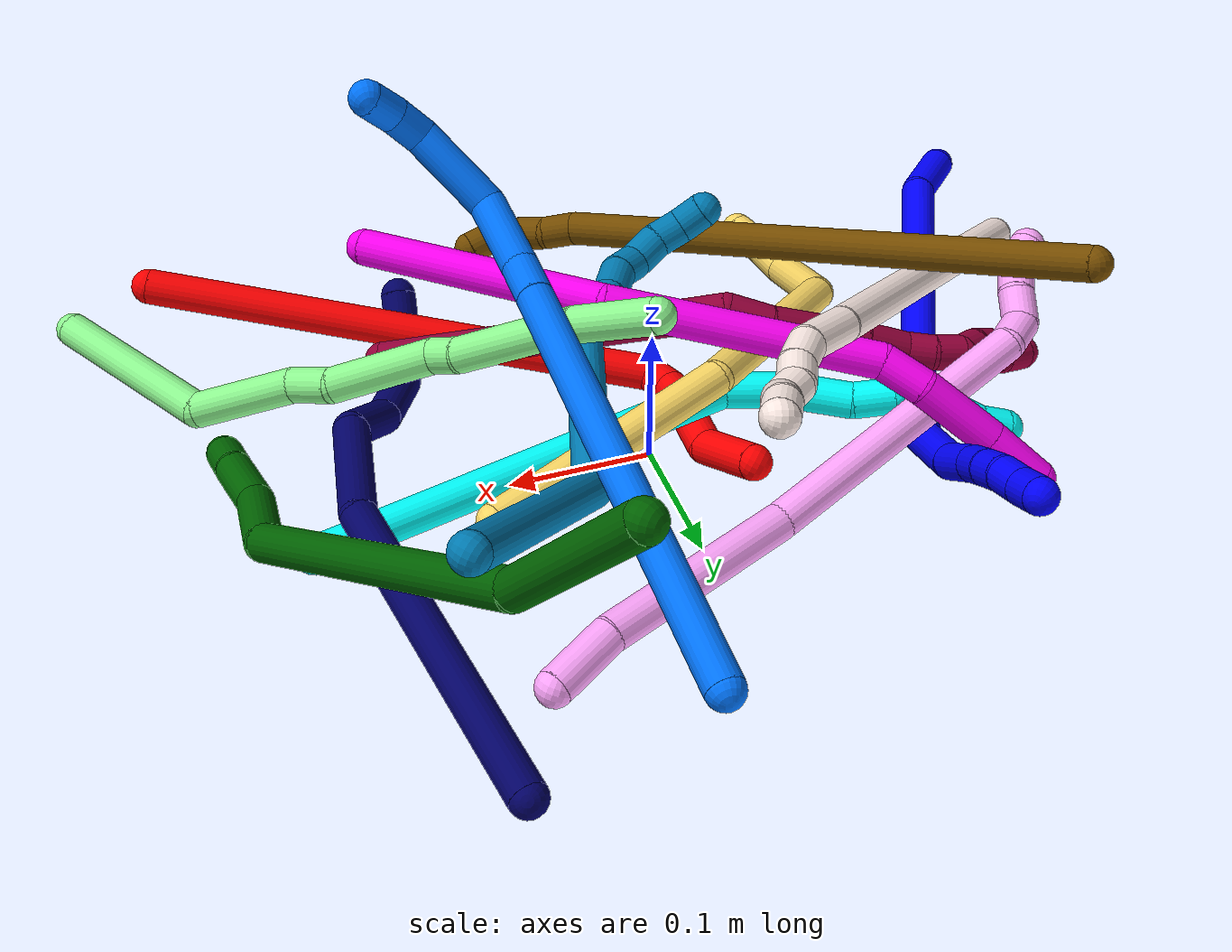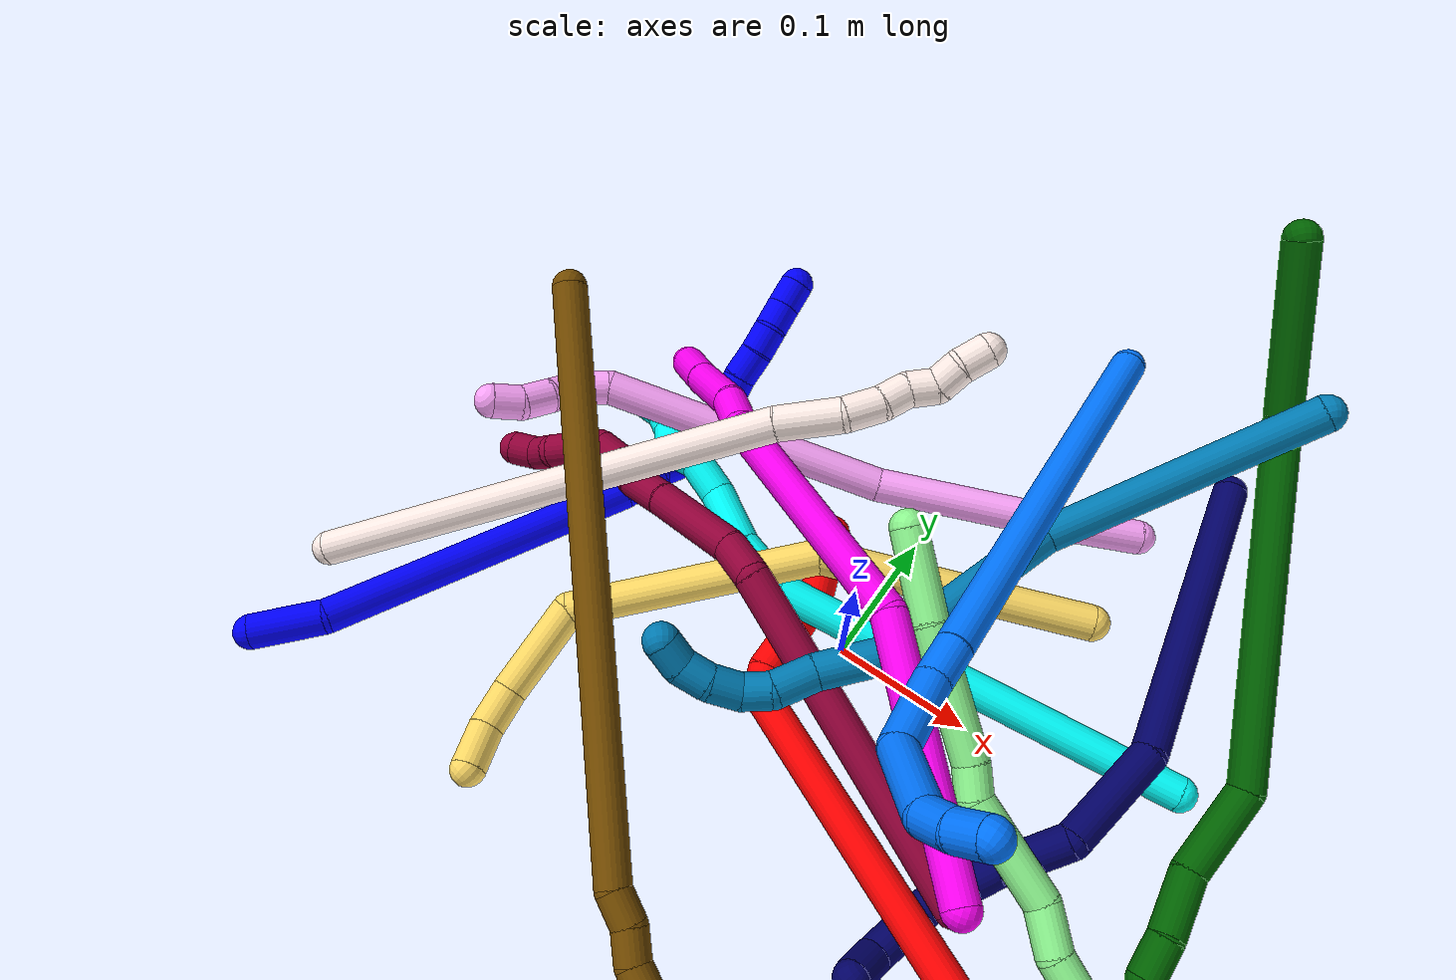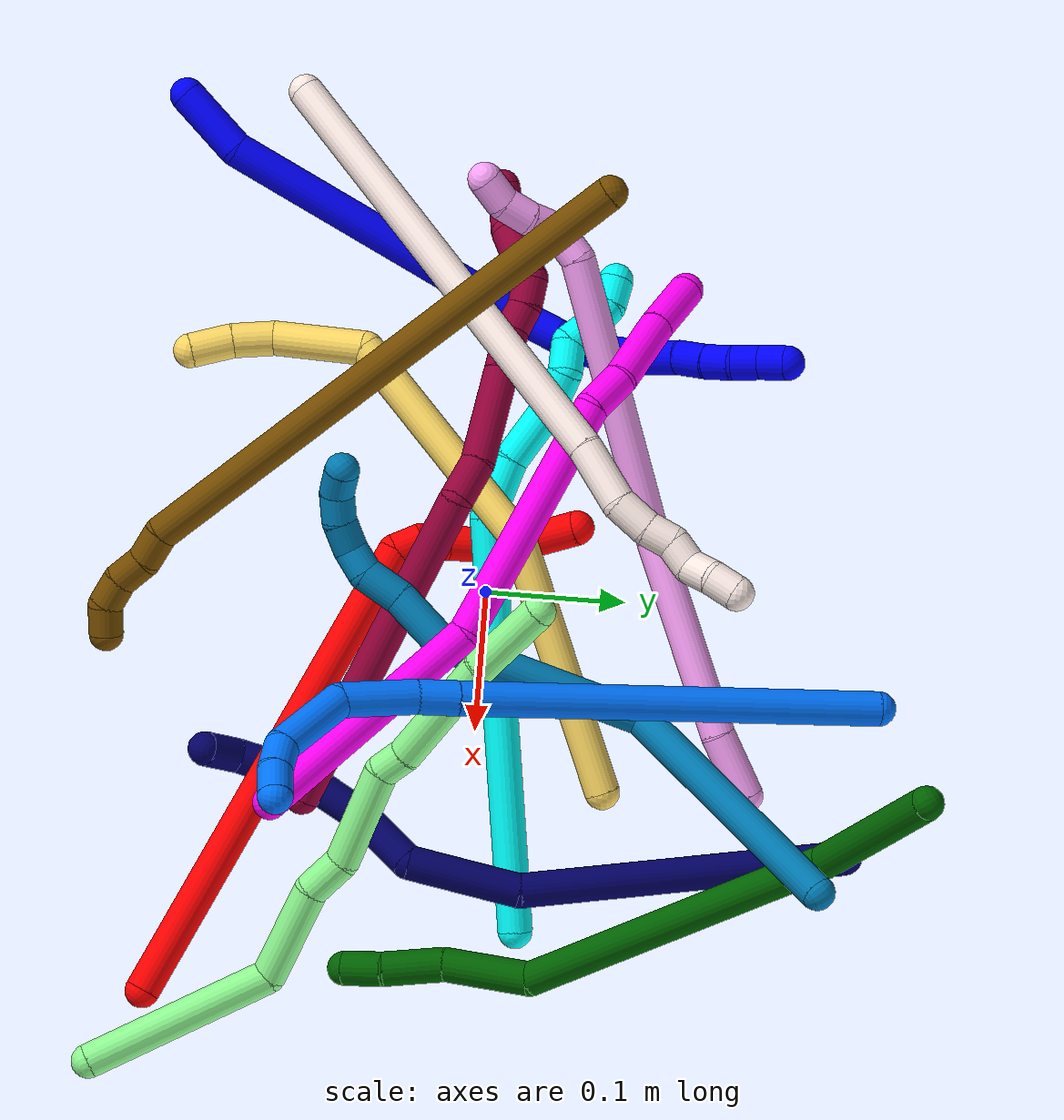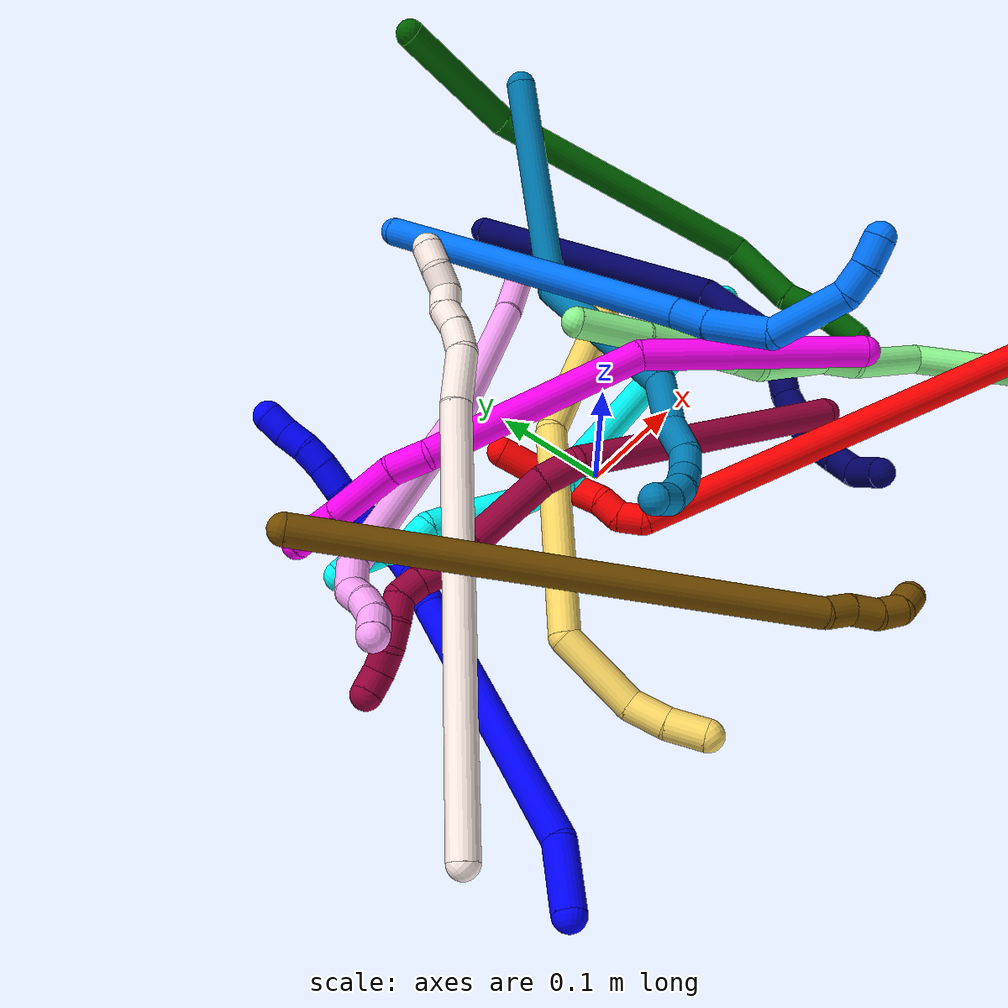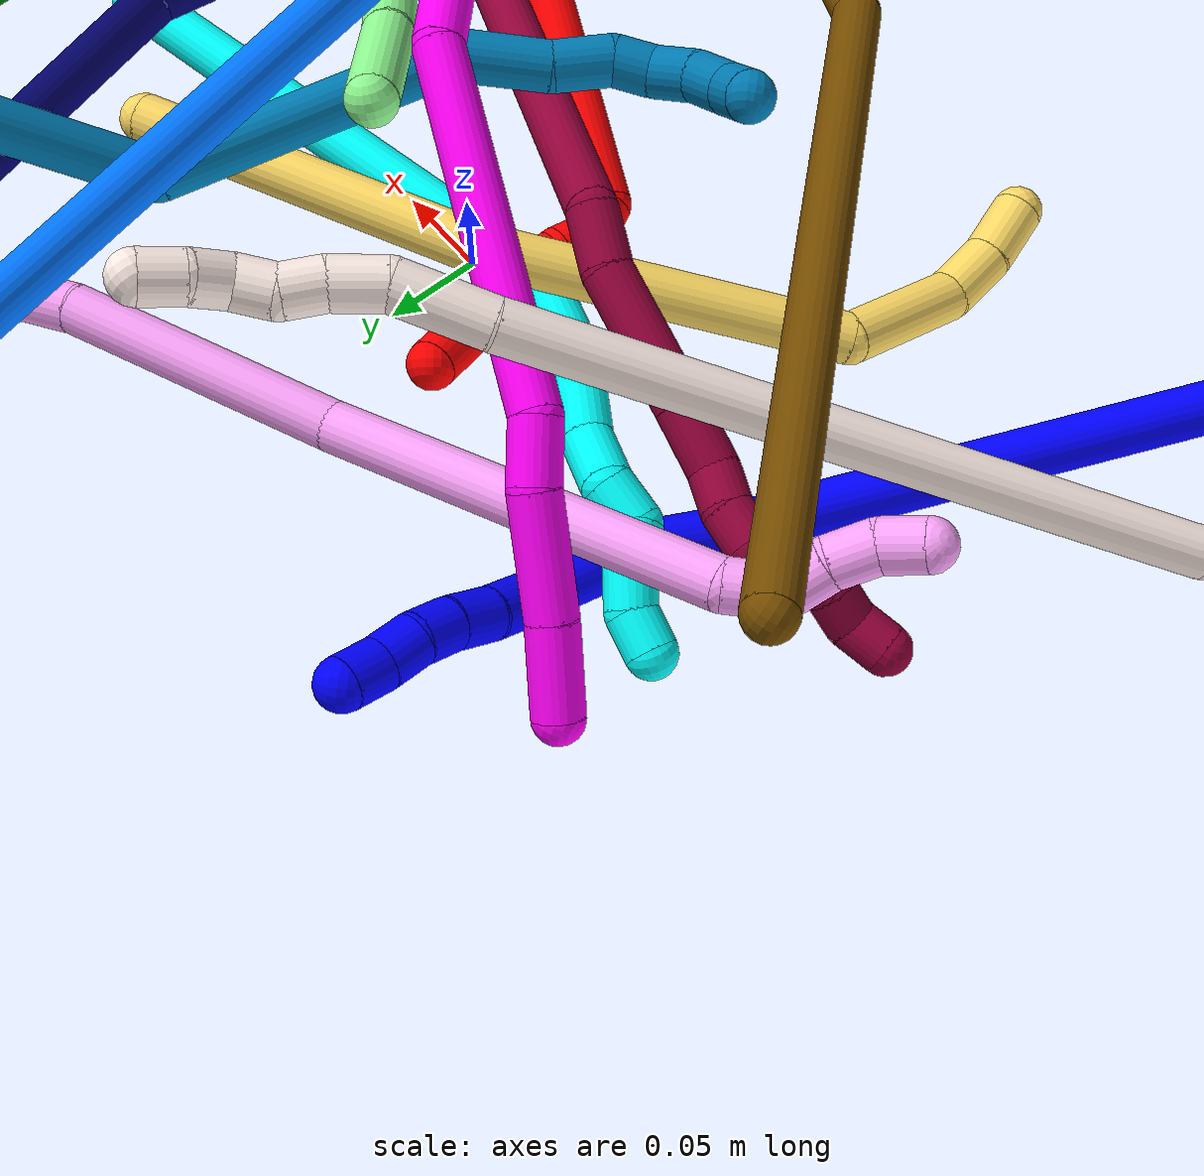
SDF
<sdf version="1.7">
 <world name="default">
  <plugin name="TubeGeneratorPlugin" filename="libtube_generator_plugin.so"/>
  <model name="photoneo_s_sensor">
   <static>1</static>
   <pose>0 0 2 1.57079 1.57079 3.14159</pose>
   <link name="link">
    <inertial><mass>0.1</mass></inertial>
    <sensor name="sensor" type="depth">
     <update_rate>30</update_rate>
     <camera>
      <horizontal_fov>1.22</horizontal_fov>
      <image><width>1920</width><height>1200</height><format>B8G8R8</format></image>
      <clip><near>0.1</near><far>4</far></clip>
      <depth_camera><output>points</output></depth_camera>
     </camera>
     <plugin name="camera_plugin" filename="libgazebo_ros_depth_camera.so">
      <baseline>0.2</baseline>
      <alwaysOn>1</alwaysOn>
      <updateRate>0.0</updateRate>
      <cameraName>camera_ir</cameraName>
      <imageTopicName>/camera/color/image_raw</imageTopicName>
      <cameraInfoTopicName>/camera/color/camera_info</cameraInfoTopicName>
      <depthImageTopicName>/camera/depth/image_raw</depthImageTopicName>
      <depthImageCameraInfoTopicName>/camera/depth/camera_info</depthImageCameraInfoTopicName>
      <pointCloudTopicName>/camera/depth/points</pointCloudTopicName>
      <frameName>fr_optical</frameName>
      <pointCloudCutoff>0.1</pointCloudCutoff>
      <pointCloudCutoffMax>2.0</pointCloudCutoffMax>
      <distortionK1>0</distortionK1>
      <distortionK2>0</distortionK2>
      <distortionK3>0</distortionK3>
      <distortionT1>0</distortionT1>
      <distortionT2>0</distortionT2>
      <CxPrime>0</CxPrime>
      <Cx>0</Cx>
      <Cy>0</Cy>
      <focalLength>0</focalLength>
      <hackBaseline>0</hackBaseline>
     </plugin>
    </sensor>
   </link>
  </model>
  <gravity>0 0 -9.8</gravity>
  <magnetic_field>6e-06 2.3e-05 -4.2e-05</magnetic_field>
  <atmosphere type="adiabatic"/>
  <physics name="default_physics" default="0" type="ode">
   <max_step_size>0.003</max_step_size>
   <real_time_factor>1</real_time_factor>
   <real_time_update_rate>1000</real_time_update_rate>
   <max_contacts>10000</max_contacts>
   <ode>
    <solver>
     <type>quick</type>
     <iters>100</iters>
     <sor>1.3</sor>
     <use_dynamic_moi_rescaling>0</use_dynamic_moi_rescaling>
    </solver>
    <constraints>
     <contact_max_correcting_vel>0</contact_max_correcting_vel>
     <contact_surface_layer>0.001</contact_surface_layer>
     <cfm>0</cfm>
     <erp>0.2</erp>
    </constraints>
   </ode>
  </physics>
  <scene><ambient>0.4 0.4 0.4 1</ambient><background>0.7 0.7 0.7 1</background><shadows>0</shadows></scene>
  <audio><device>default</device></audio>
  <spherical_coordinates>
   <surface_model>EARTH_WGS84</surface_model>
   <latitude_deg>0</latitude_deg>
   <longitude_deg>0</longitude_deg>
   <elevation>0</elevation>
   <heading_deg>0</heading_deg>
  </spherical_coordinates>
  <model name="bin">
   <static>1</static>
   <link name="bottom">
    <collision name="collision-bottom">
     <pose>0 0 -0.01 0 -0 0</pose>
     <geometry><box><size>0.8 0.6 0.02</size></box></geometry>
     <surface>
      <friction><ode><mu>100</mu><mu2>100</mu2></ode></friction>
      <contact><collide_bitmask>65535</collide_bitmask></contact>
     </surface>
    </collision>
   </link>
   <link name="west_wall">
    <collision name="collision-west_wall">
     <pose>-0.41 0 0.1 0 -0 0</pose>
     <geometry><box><size>0.02 0.6 0.2</size></box></geometry>
     <surface>
      <friction><ode><mu>100</mu><mu2>100</mu2></ode></friction>
      <contact><collide_bitmask>65535</collide_bitmask></contact>
     </surface>
    </collision>
   </link>
   <link name="east_wall">
    <collision name="collision-east_wall">
     <pose>0.41 0 0.1 0 -0 0</pose>
     <geometry><box><size>0.02 0.6 0.2</size></box></geometry>
     <surface>
      <friction><ode><mu>100</mu><mu2>100</mu2></ode></friction>
      <contact><collide_bitmask>65535</collide_bitmask></contact>
     </surface>
    </collision>
   </link>
   <link name="south_wall">
    <collision name="collision-south_wall">
     <pose>0 -0.31 0.1 0 -0 0</pose>
     <geometry><box><size>0.8 0.02 0.2</size></box></geometry>
     <surface>
      <friction><ode><mu>100</mu><mu2>100</mu2></ode></friction>
      <contact><collide_bitmask>65535</collide_bitmask></contact>
     </surface>
    </collision>
   </link>
   <link name="north_wall">
    <collision name="collision-north_wall">
     <pose>0 0.31 0.1 0 -0 0</pose>
     <geometry><box><size>0.8 0.02 0.2</size></box></geometry>
     <surface>
      <friction><ode><mu>100</mu><mu2>100</mu2></ode></friction>
      <contact><collide_bitmask>65535</collide_bitmask></contact>
     </surface>
    </collision>
   </link>
  </model>
  <model name="1">
   <static>0</static>
   <link name="1">
    <collision name="collision-cylinder-e_1_1_4">
     <pose>0.000738 0.001942 -0.026256 -3.06776 0.028031 -0.725478</pose>
     <geometry><cylinder><radius>0.0125</radius><length>0.052676</length></cylinder></geometry>
     <surface>
      <friction><ode><mu>1.16</mu><mu2>1.16</mu2><slip1>0</slip1><slip2>0</slip2></ode></friction>
      <contact><ode><kp>1e+06</kp><kd>1</kd><max_vel>0</max_vel><min_depth>0.001</min_depth></ode></contact>
     </surface>
    </collision>
    <visual name="visual-cylinder-e_1_1_4">
     <pose>0.000738 0.001942 -0.026256 -3.06776 0.028031 -0.725478</pose>
     <geometry><cylinder><radius>0.0125</radius><length>0.052676</length></cylinder></geometry>
     <material><ambient>0 0 1 1</ambient></material>
    </visual>
    <collision name="collision-cylinder-e_2_4_5">
     <pose>-0.016686 0.046294 -0.15949 -2.76416 -0.156535 0.779291</pose>
     <geometry><cylinder><radius>0.0125</radius><length>0.233006</length></cylinder></geometry>
     <surface>
      <friction><ode><mu>1.16</mu><mu2>1.16</mu2><slip1>0</slip1><slip2>0</slip2></ode></friction>
      <contact><ode><kp>1e+06</kp><kd>1</kd><max_vel>0</max_vel><min_depth>0.001</min_depth></ode></contact>
     </surface>
    </collision>
    <visual name="visual-cylinder-e_2_4_5">
     <pose>-0.016686 0.046294 -0.15949 -2.76416 -0.156535 0.779291</pose>
     <geometry><cylinder><radius>0.0125</radius><length>0.233006</length></cylinder></geometry>
     <material><ambient>0 0 1 1</ambient></material>
    </visual>
    <collision name="collision-cylinder-e_3_5_6">
     <pose>-0.033446 0.095504 -0.281239 -2.71018 0.08602 -0.387885</pose>
     <geometry><cylinder><radius>0.0125</radius><length>0.032641</length></cylinder></geometry>
     <surface>
      <friction><ode><mu>1.16</mu><mu2>1.16</mu2><slip1>0</slip1><slip2>0</slip2></ode></friction>
      <contact><ode><kp>1e+06</kp><kd>1</kd><max_vel>0</max_vel><min_depth>0.001</min_depth></ode></contact>
     </surface>
    </collision>
    <visual name="visual-cylinder-e_3_5_6">
     <pose>-0.033446 0.095504 -0.281239 -2.71018 0.08602 -0.387885</pose>
     <geometry><cylinder><radius>0.0125</radius><length>0.032641</length></cylinder></geometry>
     <material><ambient>0 0 1 1</ambient></material>
    </visual>
    <collision name="collision-cylinder-e_4_6_7">
     <pose>-0.034839 0.106486 -0.305348 -2.72046 -0.266615 1.12068</pose>
     <geometry><cylinder><radius>0.0125</radius><length>0.021215</length></cylinder></geometry>
     <surface>
      <friction><ode><mu>1.16</mu><mu2>1.16</mu2><slip1>0</slip1><slip2>0</slip2></ode></friction>
      <contact><ode><kp>1e+06</kp><kd>1</kd><max_vel>0</max_vel><min_depth>0.001</min_depth></ode></contact>
     </surface>
    </collision>
    <visual name="visual-cylinder-e_4_6_7">
     <pose>-0.034839 0.106486 -0.305348 -2.72046 -0.266615 1.12068</pose>
     <geometry><cylinder><radius>0.0125</radius><length>0.021215</length></cylinder></geometry>
     <material><ambient>0 0 1 1</ambient></material>
    </visual>
    <collision name="collision-cylinder-e_5_7_8">
     <pose>-0.03236 0.1261 -0.330931 -2.38189 0.23118 -0.566029</pose>
     <geometry><cylinder><radius>0.0125</radius><length>0.046036</length></cylinder></geometry>
     <surface>
      <friction><ode><mu>1.16</mu><mu2>1.16</mu2><slip1>0</slip1><slip2>0</slip2></ode></friction>
      <contact><ode><kp>1e+06</kp><kd>1</kd><max_vel>0</max_vel><min_depth>0.001</min_depth></ode></contact>
     </surface>
    </collision>
    <visual name="visual-cylinder-e_5_7_8">
     <pose>-0.03236 0.1261 -0.330931 -2.38189 0.23118 -0.566029</pose>
     <geometry><cylinder><radius>0.0125</radius><length>0.046036</length></cylinder></geometry>
     <material><ambient>0 0 1 1</ambient></material>
    </visual>
    <collision name="collision-cylinder-e_6_8_9">
     <pose>-0.019172 0.151913 -0.355481 -2.24547 0.536939 -1.03969</pose>
     <geometry><cylinder><radius>0.0125</radius><length>0.030942</length></cylinder></geometry>
     <surface>
      <friction><ode><mu>1.16</mu><mu2>1.16</mu2><slip1>0</slip1><slip2>0</slip2></ode></friction>
      <contact><ode><kp>1e+06</kp><kd>1</kd><max_vel>0</max_vel><min_depth>0.001</min_depth></ode></contact>
     </surface>
    </collision>
    <visual name="visual-cylinder-e_6_8_9">
     <pose>-0.019172 0.151913 -0.355481 -2.24547 0.536939 -1.03969</pose>
     <geometry><cylinder><radius>0.0125</radius><length>0.030942</length></cylinder></geometry>
     <material><ambient>0 0 1 1</ambient></material>
    </visual>
    <collision name="collision-cylinder-e_7_9_10">
     <pose>-0.005789 0.16909 -0.371214 -2.40075 0.497577 -1.15862</pose>
     <geometry><cylinder><radius>0.0125</radius><length>0.022916</length></cylinder></geometry>
     <surface>
      <friction><ode><mu>1.16</mu><mu2>1.16</mu2><slip1>0</slip1><slip2>0</slip2></ode></friction>
      <contact><ode><kp>1e+06</kp><kd>1</kd><max_vel>0</max_vel><min_depth>0.001</min_depth></ode></contact>
     </surface>
    </collision>
    <visual name="visual-cylinder-e_7_9_10">
     <pose>-0.005789 0.16909 -0.371214 -2.40075 0.497577 -1.15862</pose>
     <geometry><cylinder><radius>0.0125</radius><length>0.022916</length></cylinder></geometry>
     <material><ambient>0 0 1 1</ambient></material>
    </visual>
    <collision name="collision-cylinder-e_8_10_11">
     <pose>0.003694 0.182888 -0.384783 -2.29058 0.407026 -0.85462</pose>
     <geometry><cylinder><radius>0.0125</radius><length>0.020282</length></cylinder></geometry>
     <surface>
      <friction><ode><mu>1.16</mu><mu2>1.16</mu2><slip1>0</slip1><slip2>0</slip2></ode></friction>
      <contact><ode><kp>1e+06</kp><kd>1</kd><max_vel>0</max_vel><min_depth>0.001</min_depth></ode></contact>
     </surface>
    </collision>
    <visual name="visual-cylinder-e_8_10_11">
     <pose>0.003694 0.182888 -0.384783 -2.29058 0.407026 -0.85462</pose>
     <geometry><cylinder><radius>0.0125</radius><length>0.020282</length></cylinder></geometry>
     <material><ambient>0 0 1 1</ambient></material>
    </visual>
    <collision name="collision-cylinder-e_9_11_12">
     <pose>0.009529 0.197787 -0.396853 -2.21496 0.182217 -0.361751</pose>
     <geometry><cylinder><radius>0.0125</radius><length>0.020086</length></cylinder></geometry>
     <surface>
      <friction><ode><mu>1.16</mu><mu2>1.16</mu2><slip1>0</slip1><slip2>0</slip2></ode></friction>
      <contact><ode><kp>1e+06</kp><kd>1</kd><max_vel>0</max_vel><min_depth>0.001</min_depth></ode></contact>
     </surface>
    </collision>
    <visual name="visual-cylinder-e_9_11_12">
     <pose>0.009529 0.197787 -0.396853 -2.21496 0.182217 -0.361751</pose>
     <geometry><cylinder><radius>0.0125</radius><length>0.020086</length></cylinder></geometry>
     <material><ambient>0 0 1 1</ambient></material>
    </visual>
    <collision name="collision-cylinder-e_10_12_2">
     <pose>0.014414 0.213034 -0.408998 -2.27268 0.308344 -0.64633</pose>
     <geometry><cylinder><radius>0.0125</radius><length>0.020201</length></cylinder></geometry>
     <surface>
      <friction><ode><mu>1.16</mu><mu2>1.16</mu2><slip1>0</slip1><slip2>0</slip2></ode></friction>
      <contact><ode><kp>1e+06</kp><kd>1</kd><max_vel>0</max_vel><min_depth>0.001</min_depth></ode></contact>
     </surface>
    </collision>
    <visual name="visual-cylinder-e_10_12_2">
     <pose>0.014414 0.213034 -0.408998 -2.27268 0.308344 -0.64633</pose>
     <geometry><cylinder><radius>0.0125</radius><length>0.020201</length></cylinder></geometry>
     <material><ambient>0 0 1 1</ambient></material>
    </visual>
    <collision name="collision-sphere-2">
     <pose>0.017479 0.220383 -0.415212 0 -0 0</pose>
     <geometry><sphere><radius>0.0125</radius></sphere></geometry>
     <surface>
      <friction><ode><mu>1.16</mu><mu2>1.16</mu2><slip1>0</slip1><slip2>0</slip2></ode></friction>
      <contact><ode><kp>1e+06</kp><kd>1</kd><max_vel>0</max_vel><min_depth>0.001</min_depth></ode></contact>
     </surface>
    </collision>
    <visual name="visual-sphere-2">
     <pose>0.017479 0.220383 -0.415212 0 -0 0</pose>
     <geometry><sphere><radius>0.0125</radius></sphere></geometry>
     <material><ambient>0 0 1 1</ambient></material>
    </visual>
    <collision name="collision-sphere-12">
     <pose>0.011348 0.205685 -0.402784 0 -0 0</pose>
     <geometry><sphere><radius>0.0125</radius></sphere></geometry>
     <surface>
      <friction><ode><mu>1.16</mu><mu2>1.16</mu2><slip1>0</slip1><slip2>0</slip2></ode></friction>
      <contact><ode><kp>1e+06</kp><kd>1</kd><max_vel>0</max_vel><min_depth>0.001</min_depth></ode></contact>
     </surface>
    </collision>
    <visual name="visual-sphere-12">
     <pose>0.011348 0.205685 -0.402784 0 -0 0</pose>
     <geometry><sphere><radius>0.0125</radius></sphere></geometry>
     <material><ambient>0 0 1 1</ambient></material>
    </visual>
    <collision name="collision-sphere-11">
     <pose>0.007709 0.18989 -0.390922 0 -0 0</pose>
     <geometry><sphere><radius>0.0125</radius></sphere></geometry>
     <surface>
      <friction><ode><mu>1.16</mu><mu2>1.16</mu2><slip1>0</slip1><slip2>0</slip2></ode></friction>
      <contact><ode><kp>1e+06</kp><kd>1</kd><max_vel>0</max_vel><min_depth>0.001</min_depth></ode></contact>
     </surface>
    </collision>
    <visual name="visual-sphere-11">
     <pose>0.007709 0.18989 -0.390922 0 -0 0</pose>
     <geometry><sphere><radius>0.0125</radius></sphere></geometry>
     <material><ambient>0 0 1 1</ambient></material>
    </visual>
    <collision name="collision-sphere-10">
     <pose>-0.00032 0.175885 -0.378644 0 -0 0</pose>
     <geometry><sphere><radius>0.0125</radius></sphere></geometry>
     <surface>
      <friction><ode><mu>1.16</mu><mu2>1.16</mu2><slip1>0</slip1><slip2>0</slip2></ode></friction>
      <contact><ode><kp>1e+06</kp><kd>1</kd><max_vel>0</max_vel><min_depth>0.001</min_depth></ode></contact>
     </surface>
    </collision>
    <visual name="visual-sphere-10">
     <pose>-0.00032 0.175885 -0.378644 0 -0 0</pose>
     <geometry><sphere><radius>0.0125</radius></sphere></geometry>
     <material><ambient>0 0 1 1</ambient></material>
    </visual>
    <collision name="collision-sphere-9">
     <pose>-0.011258 0.162294 -0.363785 0 -0 0</pose>
     <geometry><sphere><radius>0.0125</radius></sphere></geometry>
     <surface>
      <friction><ode><mu>1.16</mu><mu2>1.16</mu2><slip1>0</slip1><slip2>0</slip2></ode></friction>
      <contact><ode><kp>1e+06</kp><kd>1</kd><max_vel>0</max_vel><min_depth>0.001</min_depth></ode></contact>
     </surface>
    </collision>
    <visual name="visual-sphere-9">
     <pose>-0.011258 0.162294 -0.363785 0 -0 0</pose>
     <geometry><sphere><radius>0.0125</radius></sphere></geometry>
     <material><ambient>0 0 1 1</ambient></material>
    </visual>
    <collision name="collision-sphere-4">
     <pose>0.001476 0.003884 -0.052512 0 -0 0</pose>
     <geometry><sphere><radius>0.0125</radius></sphere></geometry>
     <surface>
      <friction><ode><mu>1.16</mu><mu2>1.16</mu2><slip1>0</slip1><slip2>0</slip2></ode></friction>
      <contact><ode><kp>1e+06</kp><kd>1</kd><max_vel>0</max_vel><min_depth>0.001</min_depth></ode></contact>
     </surface>
    </collision>
    <visual name="visual-sphere-4">
     <pose>0.001476 0.003884 -0.052512 0 -0 0</pose>
     <geometry><sphere><radius>0.0125</radius></sphere></geometry>
     <material><ambient>0 0 1 1</ambient></material>
    </visual>
    <collision name="collision-sphere-1">
     <geometry><sphere><radius>0.0125</radius></sphere></geometry>
     <surface>
      <friction><ode><mu>1.16</mu><mu2>1.16</mu2><slip1>0</slip1><slip2>0</slip2></ode></friction>
      <contact><ode><kp>1e+06</kp><kd>1</kd><max_vel>0</max_vel><min_depth>0.001</min_depth></ode></contact>
     </surface>
    </collision>
    <visual name="visual-sphere-1">
     <geometry><sphere><radius>0.0125</radius></sphere></geometry>
     <material><ambient>0 0 1 1</ambient></material>
    </visual>
    <collision name="collision-sphere-8">
     <pose>-0.027085 0.141531 -0.347176 0 -0 0</pose>
     <geometry><sphere><radius>0.0125</radius></sphere></geometry>
     <surface>
      <friction><ode><mu>1.16</mu><mu2>1.16</mu2><slip1>0</slip1><slip2>0</slip2></ode></friction>
      <contact><ode><kp>1e+06</kp><kd>1</kd><max_vel>0</max_vel><min_depth>0.001</min_depth></ode></contact>
     </surface>
    </collision>
    <visual name="visual-sphere-8">
     <pose>-0.027085 0.141531 -0.347176 0 -0 0</pose>
     <geometry><sphere><radius>0.0125</radius></sphere></geometry>
     <material><ambient>0 0 1 1</ambient></material>
    </visual>
    <collision name="collision-sphere-5">
     <pose>-0.034848 0.088705 -0.266469 0 -0 0</pose>
     <geometry><sphere><radius>0.0125</radius></sphere></geometry>
     <surface>
      <friction><ode><mu>1.16</mu><mu2>1.16</mu2><slip1>0</slip1><slip2>0</slip2></ode></friction>
      <contact><ode><kp>1e+06</kp><kd>1</kd><max_vel>0</max_vel><min_depth>0.001</min_depth></ode></contact>
     </surface>
    </collision>
    <visual name="visual-sphere-5">
     <pose>-0.034848 0.088705 -0.266469 0 -0 0</pose>
     <geometry><sphere><radius>0.0125</radius></sphere></geometry>
     <material><ambient>0 0 1 1</ambient></material>
    </visual>
    <collision name="collision-sphere-6">
     <pose>-0.032044 0.102303 -0.296009 0 -0 0</pose>
     <geometry><sphere><radius>0.0125</radius></sphere></geometry>
     <surface>
      <friction><ode><mu>1.16</mu><mu2>1.16</mu2><slip1>0</slip1><slip2>0</slip2></ode></friction>
      <contact><ode><kp>1e+06</kp><kd>1</kd><max_vel>0</max_vel><min_depth>0.001</min_depth></ode></contact>
     </surface>
    </collision>
    <visual name="visual-sphere-6">
     <pose>-0.032044 0.102303 -0.296009 0 -0 0</pose>
     <geometry><sphere><radius>0.0125</radius></sphere></geometry>
     <material><ambient>0 0 1 1</ambient></material>
    </visual>
    <collision name="collision-sphere-7">
     <pose>-0.037634 0.110669 -0.314686 0 -0 0</pose>
     <geometry><sphere><radius>0.0125</radius></sphere></geometry>
     <surface>
      <friction><ode><mu>1.16</mu><mu2>1.16</mu2><slip1>0</slip1><slip2>0</slip2></ode></friction>
      <contact><ode><kp>1e+06</kp><kd>1</kd><max_vel>0</max_vel><min_depth>0.001</min_depth></ode></contact>
     </surface>
    </collision>
    <visual name="visual-sphere-7">
     <pose>-0.037634 0.110669 -0.314686 0 -0 0</pose>
     <geometry><sphere><radius>0.0125</radius></sphere></geometry>
     <material><ambient>0 0 1 1</ambient></material>
    </visual>
    <inertial>
     <pose>-0.014676 0.085263 -0.225962 0 -0 0</pose>
     <mass>0.5</mass>
     <inertia>
      <ixx>0.001494</ixx>
      <ixy>0</ixy>
      <ixz>0</ixz>
      <iyy>5.2e-05</iyy>
      <iyz>0</iyz>
      <izz>-0.000277</izz>
     </inertia>
    </inertial>
   </link>
   <pose>-0.33686 -0.240636 0.030807 2.17457 -1.50088 -1.43575</pose>
  </model>
  <model name="2">
   <static>0</static>
   <link name="2">
    <collision name="collision-cylinder-e_1_1_4">
     <pose>-0.0523 -0.021826 -0.172093 3.01544 -0.292823 -2.33225</pose>
     <geometry><cylinder><radius>0.0125</radius><length>0.362367</length></cylinder></geometry>
     <surface>
      <friction><ode><mu>1.16</mu><mu2>1.16</mu2><slip1>0</slip1><slip2>0</slip2></ode></friction>
      <contact><ode><kp>1e+06</kp><kd>1</kd><max_vel>0</max_vel><min_depth>0.001</min_depth></ode></contact>
     </surface>
    </collision>
    <visual name="visual-cylinder-e_1_1_4">
     <pose>-0.0523 -0.021826 -0.172093 3.01544 -0.292823 -2.33225</pose>
     <geometry><cylinder><radius>0.0125</radius><length>0.362367</length></cylinder></geometry>
     <material><ambient>1 0 0 1</ambient></material>
    </visual>
    <collision name="collision-cylinder-e_2_4_5">
     <pose>-0.104814 -0.038874 -0.353161 -2.65235 -0.021107 0.084507</pose>
     <geometry><cylinder><radius>0.0125</radius><length>0.02034</length></cylinder></geometry>
     <surface>
      <friction><ode><mu>1.16</mu><mu2>1.16</mu2><slip1>0</slip1><slip2>0</slip2></ode></friction>
      <contact><ode><kp>1e+06</kp><kd>1</kd><max_vel>0</max_vel><min_depth>0.001</min_depth></ode></contact>
     </surface>
    </collision>
    <visual name="visual-cylinder-e_2_4_5">
     <pose>-0.104814 -0.038874 -0.353161 -2.65235 -0.021107 0.084507</pose>
     <geometry><cylinder><radius>0.0125</radius><length>0.02034</length></cylinder></geometry>
     <material><ambient>1 0 0 1</ambient></material>
    </visual>
    <collision name="collision-cylinder-e_3_5_6">
     <pose>-0.105291 -0.025199 -0.366993 -2.07057 -0.025805 0.043486</pose>
     <geometry><cylinder><radius>0.0125</radius><length>0.02028</length></cylinder></geometry>
     <surface>
      <friction><ode><mu>1.16</mu><mu2>1.16</mu2><slip1>0</slip1><slip2>0</slip2></ode></friction>
      <contact><ode><kp>1e+06</kp><kd>1</kd><max_vel>0</max_vel><min_depth>0.001</min_depth></ode></contact>
     </surface>
    </collision>
    <visual name="visual-cylinder-e_3_5_6">
     <pose>-0.105291 -0.025199 -0.366993 -2.07057 -0.025805 0.043486</pose>
     <geometry><cylinder><radius>0.0125</radius><length>0.02028</length></cylinder></geometry>
     <material><ambient>1 0 0 1</ambient></material>
    </visual>
    <collision name="collision-cylinder-e_4_6_7">
     <pose>-0.099281 -0.000355 -0.387421 -2.34422 0.274287 -0.633202</pose>
     <geometry><cylinder><radius>0.0125</radius><length>0.046306</length></cylinder></geometry>
     <surface>
      <friction><ode><mu>1.16</mu><mu2>1.16</mu2><slip1>0</slip1><slip2>0</slip2></ode></friction>
      <contact><ode><kp>1e+06</kp><kd>1</kd><max_vel>0</max_vel><min_depth>0.001</min_depth></ode></contact>
     </surface>
    </collision>
    <visual name="visual-cylinder-e_4_6_7">
     <pose>-0.099281 -0.000355 -0.387421 -2.34422 0.274287 -0.633202</pose>
     <geometry><cylinder><radius>0.0125</radius><length>0.046306</length></cylinder></geometry>
     <material><ambient>1 0 0 1</ambient></material>
    </visual>
    <collision name="collision-cylinder-e_5_7_2">
     <pose>-0.100916 0.033316 -0.419304 -2.3148 -0.317125 0.699101</pose>
     <geometry><cylinder><radius>0.0125</radius><length>0.050707</length></cylinder></geometry>
     <surface>
      <friction><ode><mu>1.16</mu><mu2>1.16</mu2><slip1>0</slip1><slip2>0</slip2></ode></friction>
      <contact><ode><kp>1e+06</kp><kd>1</kd><max_vel>0</max_vel><min_depth>0.001</min_depth></ode></contact>
     </surface>
    </collision>
    <visual name="visual-cylinder-e_5_7_2">
     <pose>-0.100916 0.033316 -0.419304 -2.3148 -0.317125 0.699101</pose>
     <geometry><cylinder><radius>0.0125</radius><length>0.050707</length></cylinder></geometry>
     <material><ambient>1 0 0 1</ambient></material>
    </visual>
    <collision name="collision-sphere-2">
     <pose>-0.108822 0.05104 -0.435619 0 -0 0</pose>
     <geometry><sphere><radius>0.0125</radius></sphere></geometry>
     <surface>
      <friction><ode><mu>1.16</mu><mu2>1.16</mu2><slip1>0</slip1><slip2>0</slip2></ode></friction>
      <contact><ode><kp>1e+06</kp><kd>1</kd><max_vel>0</max_vel><min_depth>0.001</min_depth></ode></contact>
     </surface>
    </collision>
    <visual name="visual-sphere-2">
     <pose>-0.108822 0.05104 -0.435619 0 -0 0</pose>
     <geometry><sphere><radius>0.0125</radius></sphere></geometry>
     <material><ambient>1 0 0 1</ambient></material>
    </visual>
    <collision name="collision-sphere-7">
     <pose>-0.09301 0.015592 -0.40299 0 -0 0</pose>
     <geometry><sphere><radius>0.0125</radius></sphere></geometry>
     <surface>
      <friction><ode><mu>1.16</mu><mu2>1.16</mu2><slip1>0</slip1><slip2>0</slip2></ode></friction>
      <contact><ode><kp>1e+06</kp><kd>1</kd><max_vel>0</max_vel><min_depth>0.001</min_depth></ode></contact>
     </surface>
    </collision>
    <visual name="visual-sphere-7">
     <pose>-0.09301 0.015592 -0.40299 0 -0 0</pose>
     <geometry><sphere><radius>0.0125</radius></sphere></geometry>
     <material><ambient>1 0 0 1</ambient></material>
    </visual>
    <collision name="collision-sphere-6">
     <pose>-0.105552 -0.016302 -0.371851 0 -0 0</pose>
     <geometry><sphere><radius>0.0125</radius></sphere></geometry>
     <surface>
      <friction><ode><mu>1.16</mu><mu2>1.16</mu2><slip1>0</slip1><slip2>0</slip2></ode></friction>
      <contact><ode><kp>1e+06</kp><kd>1</kd><max_vel>0</max_vel><min_depth>0.001</min_depth></ode></contact>
     </surface>
    </collision>
    <visual name="visual-sphere-6">
     <pose>-0.105552 -0.016302 -0.371851 0 -0 0</pose>
     <geometry><sphere><radius>0.0125</radius></sphere></geometry>
     <material><ambient>1 0 0 1</ambient></material>
    </visual>
    <collision name="collision-sphere-5">
     <pose>-0.105029 -0.034095 -0.362136 0 -0 0</pose>
     <geometry><sphere><radius>0.0125</radius></sphere></geometry>
     <surface>
      <friction><ode><mu>1.16</mu><mu2>1.16</mu2><slip1>0</slip1><slip2>0</slip2></ode></friction>
      <contact><ode><kp>1e+06</kp><kd>1</kd><max_vel>0</max_vel><min_depth>0.001</min_depth></ode></contact>
     </surface>
    </collision>
    <visual name="visual-sphere-5">
     <pose>-0.105029 -0.034095 -0.362136 0 -0 0</pose>
     <geometry><sphere><radius>0.0125</radius></sphere></geometry>
     <material><ambient>1 0 0 1</ambient></material>
    </visual>
    <collision name="collision-sphere-1">
     <geometry><sphere><radius>0.0125</radius></sphere></geometry>
     <surface>
      <friction><ode><mu>1.16</mu><mu2>1.16</mu2><slip1>0</slip1><slip2>0</slip2></ode></friction>
      <contact><ode><kp>1e+06</kp><kd>1</kd><max_vel>0</max_vel><min_depth>0.001</min_depth></ode></contact>
     </surface>
    </collision>
    <visual name="visual-sphere-1">
     <geometry><sphere><radius>0.0125</radius></sphere></geometry>
     <material><ambient>1 0 0 1</ambient></material>
    </visual>
    <collision name="collision-sphere-4">
     <pose>-0.1046 -0.043653 -0.344185 0 -0 0</pose>
     <geometry><sphere><radius>0.0125</radius></sphere></geometry>
     <surface>
      <friction><ode><mu>1.16</mu><mu2>1.16</mu2><slip1>0</slip1><slip2>0</slip2></ode></friction>
      <contact><ode><kp>1e+06</kp><kd>1</kd><max_vel>0</max_vel><min_depth>0.001</min_depth></ode></contact>
     </surface>
    </collision>
    <visual name="visual-sphere-4">
     <pose>-0.1046 -0.043653 -0.344185 0 -0 0</pose>
     <geometry><sphere><radius>0.0125</radius></sphere></geometry>
     <material><ambient>1 0 0 1</ambient></material>
    </visual>
    <inertial>
     <pose>-0.065867 -0.015076 -0.232376 0 -0 0</pose>
     <mass>0.5</mass>
     <inertia>
      <ixx>-0.005373</ixx>
      <ixy>0</ixy>
      <ixz>0</ixz>
      <iyy>6.6e-05</iyy>
      <iyz>0</iyz>
      <izz>0.001577</izz>
     </inertia>
    </inertial>
   </link>
   <pose>0.30112 -0.220477 0.062808 0.88439 1.00737 0.285257</pose>
  </model>
  <model name="3">
   <static>0</static>
   <link name="3">
    <collision name="collision-cylinder-e_1_1_4">
     <pose>-0.122376 -0.035124 -0.078022 2.71859 -0.960614 -2.35977</pose>
     <geometry><cylinder><radius>0.0125</radius><length>0.298643</length></cylinder></geometry>
     <surface>
      <friction><ode><mu>1.16</mu><mu2>1.16</mu2><slip1>0</slip1><slip2>0</slip2></ode></friction>
      <contact><ode><kp>1e+06</kp><kd>1</kd><max_vel>0</max_vel><min_depth>0.001</min_depth></ode></contact>
     </surface>
    </collision>
    <visual name="visual-cylinder-e_1_1_4">
     <pose>-0.122376 -0.035124 -0.078022 2.71859 -0.960614 -2.35977</pose>
     <geometry><cylinder><radius>0.0125</radius><length>0.298643</length></cylinder></geometry>
     <material><ambient>0.003922 1 0.996078 1</ambient></material>
    </visual>
    <collision name="collision-cylinder-e_2_4_5">
     <pose>-0.261358 -0.065689 -0.169871 -2.82307 -0.850985 2.46035</pose>
     <geometry><cylinder><radius>0.0125</radius><length>0.044171</length></cylinder></geometry>
     <surface>
      <friction><ode><mu>1.16</mu><mu2>1.16</mu2><slip1>0</slip1><slip2>0</slip2></ode></friction>
      <contact><ode><kp>1e+06</kp><kd>1</kd><max_vel>0</max_vel><min_depth>0.001</min_depth></ode></contact>
     </surface>
    </collision>
    <visual name="visual-cylinder-e_2_4_5">
     <pose>-0.261358 -0.065689 -0.169871 -2.82307 -0.850985 2.46035</pose>
     <geometry><cylinder><radius>0.0125</radius><length>0.044171</length></cylinder></geometry>
     <material><ambient>0.003922 1 0.996078 1</ambient></material>
    </visual>
    <collision name="collision-cylinder-e_3_5_6">
     <pose>-0.293149 -0.051076 -0.197343 -2.50658 -0.730591 1.72194</pose>
     <geometry><cylinder><radius>0.0125</radius><length>0.045512</length></cylinder></geometry>
     <surface>
      <friction><ode><mu>1.16</mu><mu2>1.16</mu2><slip1>0</slip1><slip2>0</slip2></ode></friction>
      <contact><ode><kp>1e+06</kp><kd>1</kd><max_vel>0</max_vel><min_depth>0.001</min_depth></ode></contact>
     </surface>
    </collision>
    <visual name="visual-cylinder-e_3_5_6">
     <pose>-0.293149 -0.051076 -0.197343 -2.50658 -0.730591 1.72194</pose>
     <geometry><cylinder><radius>0.0125</radius><length>0.045512</length></cylinder></geometry>
     <material><ambient>0.003922 1 0.996078 1</ambient></material>
    </visual>
    <collision name="collision-cylinder-e_4_6_7">
     <pose>-0.320336 -0.037375 -0.21779 -2.64941 -0.999272 2.27901</pose>
     <geometry><cylinder><radius>0.0125</radius><length>0.028538</length></cylinder></geometry>
     <surface>
      <friction><ode><mu>1.16</mu><mu2>1.16</mu2><slip1>0</slip1><slip2>0</slip2></ode></friction>
      <contact><ode><kp>1e+06</kp><kd>1</kd><max_vel>0</max_vel><min_depth>0.001</min_depth></ode></contact>
     </surface>
    </collision>
    <visual name="visual-cylinder-e_4_6_7">
     <pose>-0.320336 -0.037375 -0.21779 -2.64941 -0.999272 2.27901</pose>
     <geometry><cylinder><radius>0.0125</radius><length>0.028538</length></cylinder></geometry>
     <material><ambient>0.003922 1 0.996078 1</ambient></material>
    </visual>
    <collision name="collision-cylinder-e_5_7_8">
     <pose>-0.339186 -0.034502 -0.233476 3.05466 -0.654926 -2.8869</pose>
     <geometry><cylinder><radius>0.0125</radius><length>0.022489</length></cylinder></geometry>
     <surface>
      <friction><ode><mu>1.16</mu><mu2>1.16</mu2><slip1>0</slip1><slip2>0</slip2></ode></friction>
      <contact><ode><kp>1e+06</kp><kd>1</kd><max_vel>0</max_vel><min_depth>0.001</min_depth></ode></contact>
     </surface>
    </collision>
    <visual name="visual-cylinder-e_5_7_8">
     <pose>-0.339186 -0.034502 -0.233476 3.05466 -0.654926 -2.8869</pose>
     <geometry><cylinder><radius>0.0125</radius><length>0.022489</length></cylinder></geometry>
     <material><ambient>0.003922 1 0.996078 1</ambient></material>
    </visual>
    <collision name="collision-cylinder-e_6_8_9">
     <pose>-0.35038 -0.028716 -0.248604 -2.33148 -0.447323 0.975524</pose>
     <geometry><cylinder><radius>0.0125</radius><length>0.020092</length></cylinder></geometry>
     <surface>
      <friction><ode><mu>1.16</mu><mu2>1.16</mu2><slip1>0</slip1><slip2>0</slip2></ode></friction>
      <contact><ode><kp>1e+06</kp><kd>1</kd><max_vel>0</max_vel><min_depth>0.001</min_depth></ode></contact>
     </surface>
    </collision>
    <visual name="visual-cylinder-e_6_8_9">
     <pose>-0.35038 -0.028716 -0.248604 -2.33148 -0.447323 0.975524</pose>
     <geometry><cylinder><radius>0.0125</radius><length>0.020092</length></cylinder></geometry>
     <material><ambient>0.003922 1 0.996078 1</ambient></material>
    </visual>
    <collision name="collision-cylinder-e_7_9_10">
     <pose>-0.358574 -0.01732 -0.262958 -2.60398 -0.387012 1.23661</pose>
     <geometry><cylinder><radius>0.0125</radius><length>0.02039</length></cylinder></geometry>
     <surface>
      <friction><ode><mu>1.16</mu><mu2>1.16</mu2><slip1>0</slip1><slip2>0</slip2></ode></friction>
      <contact><ode><kp>1e+06</kp><kd>1</kd><max_vel>0</max_vel><min_depth>0.001</min_depth></ode></contact>
     </surface>
    </collision>
    <visual name="visual-cylinder-e_7_9_10">
     <pose>-0.358574 -0.01732 -0.262958 -2.60398 -0.387012 1.23661</pose>
     <geometry><cylinder><radius>0.0125</radius><length>0.02039</length></cylinder></geometry>
     <material><ambient>0.003922 1 0.996078 1</ambient></material>
    </visual>
    <collision name="collision-cylinder-e_8_10_2">
     <pose>-0.368102 -0.011614 -0.279352 -3.0368 -0.59852 2.80484</pose>
     <geometry><cylinder><radius>0.0125</radius><length>0.020167</length></cylinder></geometry>
     <surface>
      <friction><ode><mu>1.16</mu><mu2>1.16</mu2><slip1>0</slip1><slip2>0</slip2></ode></friction>
      <contact><ode><kp>1e+06</kp><kd>1</kd><max_vel>0</max_vel><min_depth>0.001</min_depth></ode></contact>
     </surface>
    </collision>
    <visual name="visual-cylinder-e_8_10_2">
     <pose>-0.368102 -0.011614 -0.279352 -3.0368 -0.59852 2.80484</pose>
     <geometry><cylinder><radius>0.0125</radius><length>0.020167</length></cylinder></geometry>
     <material><ambient>0.003922 1 0.996078 1</ambient></material>
    </visual>
    <collision name="collision-sphere-2">
     <pose>-0.373784 -0.010743 -0.287636 0 -0 0</pose>
     <geometry><sphere><radius>0.0125</radius></sphere></geometry>
     <surface>
      <friction><ode><mu>1.16</mu><mu2>1.16</mu2><slip1>0</slip1><slip2>0</slip2></ode></friction>
      <contact><ode><kp>1e+06</kp><kd>1</kd><max_vel>0</max_vel><min_depth>0.001</min_depth></ode></contact>
     </surface>
    </collision>
    <visual name="visual-sphere-2">
     <pose>-0.373784 -0.010743 -0.287636 0 -0 0</pose>
     <geometry><sphere><radius>0.0125</radius></sphere></geometry>
     <material><ambient>0.003922 1 0.996078 1</ambient></material>
    </visual>
    <collision name="collision-sphere-10">
     <pose>-0.362421 -0.012486 -0.271067 0 -0 0</pose>
     <geometry><sphere><radius>0.0125</radius></sphere></geometry>
     <surface>
      <friction><ode><mu>1.16</mu><mu2>1.16</mu2><slip1>0</slip1><slip2>0</slip2></ode></friction>
      <contact><ode><kp>1e+06</kp><kd>1</kd><max_vel>0</max_vel><min_depth>0.001</min_depth></ode></contact>
     </surface>
    </collision>
    <visual name="visual-sphere-10">
     <pose>-0.362421 -0.012486 -0.271067 0 -0 0</pose>
     <geometry><sphere><radius>0.0125</radius></sphere></geometry>
     <material><ambient>0.003922 1 0.996078 1</ambient></material>
    </visual>
    <collision name="collision-sphere-9">
     <pose>-0.354726 -0.022155 -0.254849 0 -0 0</pose>
     <geometry><sphere><radius>0.0125</radius></sphere></geometry>
     <surface>
      <friction><ode><mu>1.16</mu><mu2>1.16</mu2><slip1>0</slip1><slip2>0</slip2></ode></friction>
      <contact><ode><kp>1e+06</kp><kd>1</kd><max_vel>0</max_vel><min_depth>0.001</min_depth></ode></contact>
     </surface>
    </collision>
    <visual name="visual-sphere-9">
     <pose>-0.354726 -0.022155 -0.254849 0 -0 0</pose>
     <geometry><sphere><radius>0.0125</radius></sphere></geometry>
     <material><ambient>0.003922 1 0.996078 1</ambient></material>
    </visual>
    <collision name="collision-sphere-4">
     <pose>-0.244751 -0.070248 -0.156044 0 -0 0</pose>
     <geometry><sphere><radius>0.0125</radius></sphere></geometry>
     <surface>
      <friction><ode><mu>1.16</mu><mu2>1.16</mu2><slip1>0</slip1><slip2>0</slip2></ode></friction>
      <contact><ode><kp>1e+06</kp><kd>1</kd><max_vel>0</max_vel><min_depth>0.001</min_depth></ode></contact>
     </surface>
    </collision>
    <visual name="visual-sphere-4">
     <pose>-0.244751 -0.070248 -0.156044 0 -0 0</pose>
     <geometry><sphere><radius>0.0125</radius></sphere></geometry>
     <material><ambient>0.003922 1 0.996078 1</ambient></material>
    </visual>
    <collision name="collision-sphere-1">
     <geometry><sphere><radius>0.0125</radius></sphere></geometry>
     <surface>
      <friction><ode><mu>1.16</mu><mu2>1.16</mu2><slip1>0</slip1><slip2>0</slip2></ode></friction>
      <contact><ode><kp>1e+06</kp><kd>1</kd><max_vel>0</max_vel><min_depth>0.001</min_depth></ode></contact>
     </surface>
    </collision>
    <visual name="visual-sphere-1">
     <geometry><sphere><radius>0.0125</radius></sphere></geometry>
     <material><ambient>0.003922 1 0.996078 1</ambient></material>
    </visual>
    <collision name="collision-sphere-8">
     <pose>-0.346035 -0.035276 -0.24236 0 -0 0</pose>
     <geometry><sphere><radius>0.0125</radius></sphere></geometry>
     <surface>
      <friction><ode><mu>1.16</mu><mu2>1.16</mu2><slip1>0</slip1><slip2>0</slip2></ode></friction>
      <contact><ode><kp>1e+06</kp><kd>1</kd><max_vel>0</max_vel><min_depth>0.001</min_depth></ode></contact>
     </surface>
    </collision>
    <visual name="visual-sphere-8">
     <pose>-0.346035 -0.035276 -0.24236 0 -0 0</pose>
     <geometry><sphere><radius>0.0125</radius></sphere></geometry>
     <material><ambient>0.003922 1 0.996078 1</ambient></material>
    </visual>
    <collision name="collision-sphere-5">
     <pose>-0.277964 -0.061129 -0.183699 0 -0 0</pose>
     <geometry><sphere><radius>0.0125</radius></sphere></geometry>
     <surface>
      <friction><ode><mu>1.16</mu><mu2>1.16</mu2><slip1>0</slip1><slip2>0</slip2></ode></friction>
      <contact><ode><kp>1e+06</kp><kd>1</kd><max_vel>0</max_vel><min_depth>0.001</min_depth></ode></contact>
     </surface>
    </collision>
    <visual name="visual-sphere-5">
     <pose>-0.277964 -0.061129 -0.183699 0 -0 0</pose>
     <geometry><sphere><radius>0.0125</radius></sphere></geometry>
     <material><ambient>0.003922 1 0.996078 1</ambient></material>
    </visual>
    <collision name="collision-sphere-6">
     <pose>-0.308335 -0.041022 -0.210988 0 -0 0</pose>
     <geometry><sphere><radius>0.0125</radius></sphere></geometry>
     <surface>
      <friction><ode><mu>1.16</mu><mu2>1.16</mu2><slip1>0</slip1><slip2>0</slip2></ode></friction>
      <contact><ode><kp>1e+06</kp><kd>1</kd><max_vel>0</max_vel><min_depth>0.001</min_depth></ode></contact>
     </surface>
    </collision>
    <visual name="visual-sphere-6">
     <pose>-0.308335 -0.041022 -0.210988 0 -0 0</pose>
     <geometry><sphere><radius>0.0125</radius></sphere></geometry>
     <material><ambient>0.003922 1 0.996078 1</ambient></material>
    </visual>
    <collision name="collision-sphere-7">
     <pose>-0.332337 -0.033728 -0.224592 0 -0 0</pose>
     <geometry><sphere><radius>0.0125</radius></sphere></geometry>
     <surface>
      <friction><ode><mu>1.16</mu><mu2>1.16</mu2><slip1>0</slip1><slip2>0</slip2></ode></friction>
      <contact><ode><kp>1e+06</kp><kd>1</kd><max_vel>0</max_vel><min_depth>0.001</min_depth></ode></contact>
     </surface>
    </collision>
    <visual name="visual-sphere-7">
     <pose>-0.332337 -0.033728 -0.224592 0 -0 0</pose>
     <geometry><sphere><radius>0.0125</radius></sphere></geometry>
     <material><ambient>0.003922 1 0.996078 1</ambient></material>
    </visual>
    <inertial>
     <pose>-0.199953 -0.037445 -0.134483 0 -0 0</pose>
     <mass>0.5</mass>
     <inertia>
      <ixx>-0.001831</ixx>
      <ixy>0</ixy>
      <ixz>0</ixz>
      <iyy>0.001104</iyy>
      <iyz>0</iyz>
      <izz>0.002341</izz>
     </inertia>
    </inertial>
   </link>
   <pose>0.241158 0.039985 0.012428 0.073349 0.677637 -0.052601</pose>
  </model>
  <model name="4">
   <static>0</static>
   <link name="4">
    <collision name="collision-cylinder-e_1_1_4">
     <pose>-0.01867 -0.004927 -0.015165 2.82747 -0.863948 -2.47982</pose>
     <geometry><cylinder><radius>0.0125</radius><length>0.049105</length></cylinder></geometry>
     <surface>
      <friction><ode><mu>1.16</mu><mu2>1.16</mu2><slip1>0</slip1><slip2>0</slip2></ode></friction>
      <contact><ode><kp>1e+06</kp><kd>1</kd><max_vel>0</max_vel><min_depth>0.001</min_depth></ode></contact>
     </surface>
    </collision>
    <visual name="visual-cylinder-e_1_1_4">
     <pose>-0.01867 -0.004927 -0.015165 2.82747 -0.863948 -2.47982</pose>
     <geometry><cylinder><radius>0.0125</radius><length>0.049105</length></cylinder></geometry>
     <material><ambient>1 0.65098 0.996078 1</ambient></material>
    </visual>
    <collision name="collision-cylinder-e_2_4_5">
     <pose>-0.095753 -0.033942 -0.067666 2.56862 -0.920515 -2.06929</pose>
     <geometry><cylinder><radius>0.0125</radius><length>0.146781</length></cylinder></geometry>
     <surface>
      <friction><ode><mu>1.16</mu><mu2>1.16</mu2><slip1>0</slip1><slip2>0</slip2></ode></friction>
      <contact><ode><kp>1e+06</kp><kd>1</kd><max_vel>0</max_vel><min_depth>0.001</min_depth></ode></contact>
     </surface>
    </collision>
    <visual name="visual-cylinder-e_2_4_5">
     <pose>-0.095753 -0.033942 -0.067666 2.56862 -0.920515 -2.06929</pose>
     <geometry><cylinder><radius>0.0125</radius><length>0.146781</length></cylinder></geometry>
     <material><ambient>1 0.65098 0.996078 1</ambient></material>
    </visual>
    <collision name="collision-cylinder-e_3_5_6">
     <pose>-0.224646 -0.094255 -0.174814 2.66294 -0.73066 -2.00592</pose>
     <geometry><cylinder><radius>0.0125</radius><length>0.21122</length></cylinder></geometry>
     <surface>
      <friction><ode><mu>1.16</mu><mu2>1.16</mu2><slip1>0</slip1><slip2>0</slip2></ode></friction>
      <contact><ode><kp>1e+06</kp><kd>1</kd><max_vel>0</max_vel><min_depth>0.001</min_depth></ode></contact>
     </surface>
    </collision>
    <visual name="visual-cylinder-e_3_5_6">
     <pose>-0.224646 -0.094255 -0.174814 2.66294 -0.73066 -2.00592</pose>
     <geometry><cylinder><radius>0.0125</radius><length>0.21122</length></cylinder></geometry>
     <material><ambient>1 0.65098 0.996078 1</ambient></material>
    </visual>
    <collision name="collision-cylinder-e_4_6_7">
     <pose>-0.306135 -0.130608 -0.251183 3.12215 -1.03352 -3.10739</pose>
     <geometry><cylinder><radius>0.0125</radius><length>0.02563</length></cylinder></geometry>
     <surface>
      <friction><ode><mu>1.16</mu><mu2>1.16</mu2><slip1>0</slip1><slip2>0</slip2></ode></friction>
      <contact><ode><kp>1e+06</kp><kd>1</kd><max_vel>0</max_vel><min_depth>0.001</min_depth></ode></contact>
     </surface>
    </collision>
    <visual name="visual-cylinder-e_4_6_7">
     <pose>-0.306135 -0.130608 -0.251183 3.12215 -1.03352 -3.10739</pose>
     <geometry><cylinder><radius>0.0125</radius><length>0.02563</length></cylinder></geometry>
     <material><ambient>1 0.65098 0.996078 1</ambient></material>
    </visual>
    <collision name="collision-cylinder-e_5_7_8">
     <pose>-0.322543 -0.124767 -0.266241 -2.52947 -0.47933 1.31652</pose>
     <geometry><cylinder><radius>0.0125</radius><length>0.023412</length></cylinder></geometry>
     <surface>
      <friction><ode><mu>1.16</mu><mu2>1.16</mu2><slip1>0</slip1><slip2>0</slip2></ode></friction>
      <contact><ode><kp>1e+06</kp><kd>1</kd><max_vel>0</max_vel><min_depth>0.001</min_depth></ode></contact>
     </surface>
    </collision>
    <visual name="visual-cylinder-e_5_7_8">
     <pose>-0.322543 -0.124767 -0.266241 -2.52947 -0.47933 1.31652</pose>
     <geometry><cylinder><radius>0.0125</radius><length>0.023412</length></cylinder></geometry>
     <material><ambient>1 0.65098 0.996078 1</ambient></material>
    </visual>
    <collision name="collision-cylinder-e_6_8_9">
     <pose>-0.335252 -0.114433 -0.281891 -2.59332 -0.717538 1.85469</pose>
     <geometry><cylinder><radius>0.0125</radius><length>0.022235</length></cylinder></geometry>
     <surface>
      <friction><ode><mu>1.16</mu><mu2>1.16</mu2><slip1>0</slip1><slip2>0</slip2></ode></friction>
      <contact><ode><kp>1e+06</kp><kd>1</kd><max_vel>0</max_vel><min_depth>0.001</min_depth></ode></contact>
     </surface>
    </collision>
    <visual name="visual-cylinder-e_6_8_9">
     <pose>-0.335252 -0.114433 -0.281891 -2.59332 -0.717538 1.85469</pose>
     <geometry><cylinder><radius>0.0125</radius><length>0.022235</length></cylinder></geometry>
     <material><ambient>1 0.65098 0.996078 1</ambient></material>
    </visual>
    <collision name="collision-cylinder-e_7_9_2">
     <pose>-0.350124 -0.109704 -0.296753 -3.09458 -0.774888 3.02649</pose>
     <geometry><cylinder><radius>0.0125</radius><length>0.021616</length></cylinder></geometry>
     <surface>
      <friction><ode><mu>1.16</mu><mu2>1.16</mu2><slip1>0</slip1><slip2>0</slip2></ode></friction>
      <contact><ode><kp>1e+06</kp><kd>1</kd><max_vel>0</max_vel><min_depth>0.001</min_depth></ode></contact>
     </surface>
    </collision>
    <visual name="visual-cylinder-e_7_9_2">
     <pose>-0.350124 -0.109704 -0.296753 -3.09458 -0.774888 3.02649</pose>
     <geometry><cylinder><radius>0.0125</radius><length>0.021616</length></cylinder></geometry>
     <material><ambient>1 0.65098 0.996078 1</ambient></material>
    </visual>
    <collision name="collision-sphere-2">
     <pose>-0.357686 -0.109341 -0.304467 0 -0 0</pose>
     <geometry><sphere><radius>0.0125</radius></sphere></geometry>
     <surface>
      <friction><ode><mu>1.16</mu><mu2>1.16</mu2><slip1>0</slip1><slip2>0</slip2></ode></friction>
      <contact><ode><kp>1e+06</kp><kd>1</kd><max_vel>0</max_vel><min_depth>0.001</min_depth></ode></contact>
     </surface>
    </collision>
    <visual name="visual-sphere-2">
     <pose>-0.357686 -0.109341 -0.304467 0 -0 0</pose>
     <geometry><sphere><radius>0.0125</radius></sphere></geometry>
     <material><ambient>1 0.65098 0.996078 1</ambient></material>
    </visual>
    <collision name="collision-sphere-9">
     <pose>-0.342562 -0.110067 -0.289039 0 -0 0</pose>
     <geometry><sphere><radius>0.0125</radius></sphere></geometry>
     <surface>
      <friction><ode><mu>1.16</mu><mu2>1.16</mu2><slip1>0</slip1><slip2>0</slip2></ode></friction>
      <contact><ode><kp>1e+06</kp><kd>1</kd><max_vel>0</max_vel><min_depth>0.001</min_depth></ode></contact>
     </surface>
    </collision>
    <visual name="visual-sphere-9">
     <pose>-0.342562 -0.110067 -0.289039 0 -0 0</pose>
     <geometry><sphere><radius>0.0125</radius></sphere></geometry>
     <material><ambient>1 0.65098 0.996078 1</ambient></material>
    </visual>
    <collision name="collision-sphere-4">
     <pose>-0.03734 -0.009854 -0.030331 0 -0 0</pose>
     <geometry><sphere><radius>0.0125</radius></sphere></geometry>
     <surface>
      <friction><ode><mu>1.16</mu><mu2>1.16</mu2><slip1>0</slip1><slip2>0</slip2></ode></friction>
      <contact><ode><kp>1e+06</kp><kd>1</kd><max_vel>0</max_vel><min_depth>0.001</min_depth></ode></contact>
     </surface>
    </collision>
    <visual name="visual-sphere-4">
     <pose>-0.03734 -0.009854 -0.030331 0 -0 0</pose>
     <geometry><sphere><radius>0.0125</radius></sphere></geometry>
     <material><ambient>1 0.65098 0.996078 1</ambient></material>
    </visual>
    <collision name="collision-sphere-1">
     <geometry><sphere><radius>0.0125</radius></sphere></geometry>
     <surface>
      <friction><ode><mu>1.16</mu><mu2>1.16</mu2><slip1>0</slip1><slip2>0</slip2></ode></friction>
      <contact><ode><kp>1e+06</kp><kd>1</kd><max_vel>0</max_vel><min_depth>0.001</min_depth></ode></contact>
     </surface>
    </collision>
    <visual name="visual-sphere-1">
     <geometry><sphere><radius>0.0125</radius></sphere></geometry>
     <material><ambient>1 0.65098 0.996078 1</ambient></material>
    </visual>
    <collision name="collision-sphere-8">
     <pose>-0.327942 -0.118799 -0.274742 0 -0 0</pose>
     <geometry><sphere><radius>0.0125</radius></sphere></geometry>
     <surface>
      <friction><ode><mu>1.16</mu><mu2>1.16</mu2><slip1>0</slip1><slip2>0</slip2></ode></friction>
      <contact><ode><kp>1e+06</kp><kd>1</kd><max_vel>0</max_vel><min_depth>0.001</min_depth></ode></contact>
     </surface>
    </collision>
    <visual name="visual-sphere-8">
     <pose>-0.327942 -0.118799 -0.274742 0 -0 0</pose>
     <geometry><sphere><radius>0.0125</radius></sphere></geometry>
     <material><ambient>1 0.65098 0.996078 1</ambient></material>
    </visual>
    <collision name="collision-sphere-5">
     <pose>-0.154166 -0.058029 -0.105001 0 -0 0</pose>
     <geometry><sphere><radius>0.0125</radius></sphere></geometry>
     <surface>
      <friction><ode><mu>1.16</mu><mu2>1.16</mu2><slip1>0</slip1><slip2>0</slip2></ode></friction>
      <contact><ode><kp>1e+06</kp><kd>1</kd><max_vel>0</max_vel><min_depth>0.001</min_depth></ode></contact>
     </surface>
    </collision>
    <visual name="visual-sphere-5">
     <pose>-0.154166 -0.058029 -0.105001 0 -0 0</pose>
     <geometry><sphere><radius>0.0125</radius></sphere></geometry>
     <material><ambient>1 0.65098 0.996078 1</ambient></material>
    </visual>
    <collision name="collision-sphere-6">
     <pose>-0.295126 -0.130481 -0.244626 0 -0 0</pose>
     <geometry><sphere><radius>0.0125</radius></sphere></geometry>
     <surface>
      <friction><ode><mu>1.16</mu><mu2>1.16</mu2><slip1>0</slip1><slip2>0</slip2></ode></friction>
      <contact><ode><kp>1e+06</kp><kd>1</kd><max_vel>0</max_vel><min_depth>0.001</min_depth></ode></contact>
     </surface>
    </collision>
    <visual name="visual-sphere-6">
     <pose>-0.295126 -0.130481 -0.244626 0 -0 0</pose>
     <geometry><sphere><radius>0.0125</radius></sphere></geometry>
     <material><ambient>1 0.65098 0.996078 1</ambient></material>
    </visual>
    <collision name="collision-sphere-7">
     <pose>-0.317144 -0.130736 -0.25774 0 -0 0</pose>
     <geometry><sphere><radius>0.0125</radius></sphere></geometry>
     <surface>
      <friction><ode><mu>1.16</mu><mu2>1.16</mu2><slip1>0</slip1><slip2>0</slip2></ode></friction>
      <contact><ode><kp>1e+06</kp><kd>1</kd><max_vel>0</max_vel><min_depth>0.001</min_depth></ode></contact>
     </surface>
    </collision>
    <visual name="visual-sphere-7">
     <pose>-0.317144 -0.130736 -0.25774 0 -0 0</pose>
     <geometry><sphere><radius>0.0125</radius></sphere></geometry>
     <material><ambient>1 0.65098 0.996078 1</ambient></material>
    </visual>
    <inertial>
     <pose>-0.185683 -0.072634 -0.145909 0 -0 0</pose>
     <mass>0.5</mass>
     <inertia>
      <ixx>-0.001044</ixx>
      <ixy>0</ixy>
      <ixz>0</ixz>
      <iyy>5.5e-05</iyy>
      <iyz>0</iyz>
      <izz>0.001096</izz>
     </inertia>
    </inertial>
   </link>
   <pose>0.131091 0.197204 0.012508 3.00107 -0.491056 0.806569</pose>
  </model>
  <model name="5">
   <static>0</static>
   <link name="5">
    <collision name="collision-cylinder-e_1_1_4">
     <pose>-0.072789 -0.035093 0.049323 0.618405 -0.877063 -0.297423</pose>
     <geometry><cylinder><radius>0.0125</radius><length>0.18934</length></cylinder></geometry>
     <surface>
      <friction><ode><mu>1.16</mu><mu2>1.16</mu2><slip1>0</slip1><slip2>0</slip2></ode></friction>
      <contact><ode><kp>1e+06</kp><kd>1</kd><max_vel>0</max_vel><min_depth>0.001</min_depth></ode></contact>
     </surface>
    </collision>
    <visual name="visual-cylinder-e_1_1_4">
     <pose>-0.072789 -0.035093 0.049323 0.618405 -0.877063 -0.297423</pose>
     <geometry><cylinder><radius>0.0125</radius><length>0.18934</length></cylinder></geometry>
     <material><ambient>1 0.858824 0.4 1</ambient></material>
    </visual>
    <collision name="collision-cylinder-e_2_4_5">
     <pose>-0.183502 -0.104331 0.17247 0.433206 -0.436295 -0.097484</pose>
     <geometry><cylinder><radius>0.0125</radius><length>0.179491</length></cylinder></geometry>
     <surface>
      <friction><ode><mu>1.16</mu><mu2>1.16</mu2><slip1>0</slip1><slip2>0</slip2></ode></friction>
      <contact><ode><kp>1e+06</kp><kd>1</kd><max_vel>0</max_vel><min_depth>0.001</min_depth></ode></contact>
     </surface>
    </collision>
    <visual name="visual-cylinder-e_2_4_5">
     <pose>-0.183502 -0.104331 0.17247 0.433206 -0.436295 -0.097484</pose>
     <geometry><cylinder><radius>0.0125</radius><length>0.179491</length></cylinder></geometry>
     <material><ambient>1 0.858824 0.4 1</ambient></material>
    </visual>
    <collision name="collision-cylinder-e_3_5_6">
     <pose>-0.21602 -0.136983 0.280519 -0.043579 0.156543 -0.003419</pose>
     <geometry><cylinder><radius>0.0125</radius><length>0.069361</length></cylinder></geometry>
     <surface>
      <friction><ode><mu>1.16</mu><mu2>1.16</mu2><slip1>0</slip1><slip2>0</slip2></ode></friction>
      <contact><ode><kp>1e+06</kp><kd>1</kd><max_vel>0</max_vel><min_depth>0.001</min_depth></ode></contact>
     </surface>
    </collision>
    <visual name="visual-cylinder-e_3_5_6">
     <pose>-0.21602 -0.136983 0.280519 -0.043579 0.156543 -0.003419</pose>
     <geometry><cylinder><radius>0.0125</radius><length>0.069361</length></cylinder></geometry>
     <material><ambient>1 0.858824 0.4 1</ambient></material>
    </visual>
    <collision name="collision-cylinder-e_4_6_7">
     <pose>-0.209245 -0.129231 0.328776 -0.419599 0.088834 -0.018928</pose>
     <geometry><cylinder><radius>0.0125</radius><length>0.030853</length></cylinder></geometry>
     <surface>
      <friction><ode><mu>1.16</mu><mu2>1.16</mu2><slip1>0</slip1><slip2>0</slip2></ode></friction>
      <contact><ode><kp>1e+06</kp><kd>1</kd><max_vel>0</max_vel><min_depth>0.001</min_depth></ode></contact>
     </surface>
    </collision>
    <visual name="visual-cylinder-e_4_6_7">
     <pose>-0.209245 -0.129231 0.328776 -0.419599 0.088834 -0.018928</pose>
     <geometry><cylinder><radius>0.0125</radius><length>0.030853</length></cylinder></geometry>
     <material><ambient>1 0.858824 0.4 1</ambient></material>
    </visual>
    <collision name="collision-cylinder-e_5_7_2">
     <pose>-0.205231 -0.114464 0.355464 -0.591793 0.171791 -0.052487</pose>
     <geometry><cylinder><radius>0.0125</radius><length>0.030955</length></cylinder></geometry>
     <surface>
      <friction><ode><mu>1.16</mu><mu2>1.16</mu2><slip1>0</slip1><slip2>0</slip2></ode></friction>
      <contact><ode><kp>1e+06</kp><kd>1</kd><max_vel>0</max_vel><min_depth>0.001</min_depth></ode></contact>
     </surface>
    </collision>
    <visual name="visual-cylinder-e_5_7_2">
     <pose>-0.205231 -0.114464 0.355464 -0.591793 0.171791 -0.052487</pose>
     <geometry><cylinder><radius>0.0125</radius><length>0.030955</length></cylinder></geometry>
     <material><ambient>1 0.858824 0.4 1</ambient></material>
    </visual>
    <collision name="collision-sphere-2">
     <pose>-0.202585 -0.105958 0.368121 0 -0 0</pose>
     <geometry><sphere><radius>0.0125</radius></sphere></geometry>
     <surface>
      <friction><ode><mu>1.16</mu><mu2>1.16</mu2><slip1>0</slip1><slip2>0</slip2></ode></friction>
      <contact><ode><kp>1e+06</kp><kd>1</kd><max_vel>0</max_vel><min_depth>0.001</min_depth></ode></contact>
     </surface>
    </collision>
    <visual name="visual-sphere-2">
     <pose>-0.202585 -0.105958 0.368121 0 -0 0</pose>
     <geometry><sphere><radius>0.0125</radius></sphere></geometry>
     <material><ambient>1 0.858824 0.4 1</ambient></material>
    </visual>
    <collision name="collision-sphere-7">
     <pose>-0.207876 -0.122971 0.342808 0 -0 0</pose>
     <geometry><sphere><radius>0.0125</radius></sphere></geometry>
     <surface>
      <friction><ode><mu>1.16</mu><mu2>1.16</mu2><slip1>0</slip1><slip2>0</slip2></ode></friction>
      <contact><ode><kp>1e+06</kp><kd>1</kd><max_vel>0</max_vel><min_depth>0.001</min_depth></ode></contact>
     </surface>
    </collision>
    <visual name="visual-sphere-7">
     <pose>-0.207876 -0.122971 0.342808 0 -0 0</pose>
     <geometry><sphere><radius>0.0125</radius></sphere></geometry>
     <material><ambient>1 0.858824 0.4 1</ambient></material>
    </visual>
    <collision name="collision-sphere-6">
     <pose>-0.210614 -0.135491 0.314743 0 -0 0</pose>
     <geometry><sphere><radius>0.0125</radius></sphere></geometry>
     <surface>
      <friction><ode><mu>1.16</mu><mu2>1.16</mu2><slip1>0</slip1><slip2>0</slip2></ode></friction>
      <contact><ode><kp>1e+06</kp><kd>1</kd><max_vel>0</max_vel><min_depth>0.001</min_depth></ode></contact>
     </surface>
    </collision>
    <visual name="visual-sphere-6">
     <pose>-0.210614 -0.135491 0.314743 0 -0 0</pose>
     <geometry><sphere><radius>0.0125</radius></sphere></geometry>
     <material><ambient>1 0.858824 0.4 1</ambient></material>
    </visual>
    <collision name="collision-sphere-5">
     <pose>-0.221427 -0.138476 0.246295 0 -0 0</pose>
     <geometry><sphere><radius>0.0125</radius></sphere></geometry>
     <surface>
      <friction><ode><mu>1.16</mu><mu2>1.16</mu2><slip1>0</slip1><slip2>0</slip2></ode></friction>
      <contact><ode><kp>1e+06</kp><kd>1</kd><max_vel>0</max_vel><min_depth>0.001</min_depth></ode></contact>
     </surface>
    </collision>
    <visual name="visual-sphere-5">
     <pose>-0.221427 -0.138476 0.246295 0 -0 0</pose>
     <geometry><sphere><radius>0.0125</radius></sphere></geometry>
     <material><ambient>1 0.858824 0.4 1</ambient></material>
    </visual>
    <collision name="collision-sphere-1">
     <geometry><sphere><radius>0.0125</radius></sphere></geometry>
     <surface>
      <friction><ode><mu>1.16</mu><mu2>1.16</mu2><slip1>0</slip1><slip2>0</slip2></ode></friction>
      <contact><ode><kp>1e+06</kp><kd>1</kd><max_vel>0</max_vel><min_depth>0.001</min_depth></ode></contact>
     </surface>
    </collision>
    <visual name="visual-sphere-1">
     <geometry><sphere><radius>0.0125</radius></sphere></geometry>
     <material><ambient>1 0.858824 0.4 1</ambient></material>
    </visual>
    <collision name="collision-sphere-4">
     <pose>-0.145577 -0.070187 0.098645 0 -0 0</pose>
     <geometry><sphere><radius>0.0125</radius></sphere></geometry>
     <surface>
      <friction><ode><mu>1.16</mu><mu2>1.16</mu2><slip1>0</slip1><slip2>0</slip2></ode></friction>
      <contact><ode><kp>1e+06</kp><kd>1</kd><max_vel>0</max_vel><min_depth>0.001</min_depth></ode></contact>
     </surface>
    </collision>
    <visual name="visual-sphere-4">
     <pose>-0.145577 -0.070187 0.098645 0 -0 0</pose>
     <geometry><sphere><radius>0.0125</radius></sphere></geometry>
     <material><ambient>1 0.858824 0.4 1</ambient></material>
    </visual>
    <inertial>
     <pose>-0.149022 -0.084806 0.161799 0 -0 0</pose>
     <mass>0.5</mass>
     <inertia>
      <ixx>0.000662</ixx>
      <ixy>0</ixy>
      <ixz>0</ixz>
      <iyy>0.000849</iyy>
      <iyz>0</iyz>
      <izz>0.001064</izz>
     </inertia>
    </inertial>
   </link>
   <pose>0.135553 0.093456 0.056203 1.8992 0.684916 0.013332</pose>
  </model>
  <model name="6">
   <static>0</static>
   <link name="6">
    <collision name="collision-cylinder-e_1_1_4">
     <pose>-0.015894 -0.036842 -0.04217 2.42353 -0.27656 -0.710202</pose>
     <geometry><cylinder><radius>0.0125</radius><length>0.116418</length></cylinder></geometry>
     <surface>
      <friction><ode><mu>1.16</mu><mu2>1.16</mu2><slip1>0</slip1><slip2>0</slip2></ode></friction>
      <contact><ode><kp>1e+06</kp><kd>1</kd><max_vel>0</max_vel><min_depth>0.001</min_depth></ode></contact>
     </surface>
    </collision>
    <visual name="visual-cylinder-e_1_1_4">
     <pose>-0.015894 -0.036842 -0.04217 2.42353 -0.27656 -0.710202</pose>
     <geometry><cylinder><radius>0.0125</radius><length>0.116418</length></cylinder></geometry>
     <material><ambient>0 0.392157 0.003922 1</ambient></material>
    </visual>
    <collision name="collision-cylinder-e_2_4_5">
     <pose>-0.033679 -0.121548 -0.197369 2.74102 -0.015405 -0.075851</pose>
     <geometry><cylinder><radius>0.0125</radius><length>0.245519</length></cylinder></geometry>
     <surface>
      <friction><ode><mu>1.16</mu><mu2>1.16</mu2><slip1>0</slip1><slip2>0</slip2></ode></friction>
      <contact><ode><kp>1e+06</kp><kd>1</kd><max_vel>0</max_vel><min_depth>0.001</min_depth></ode></contact>
     </surface>
    </collision>
    <visual name="visual-cylinder-e_2_4_5">
     <pose>-0.033679 -0.121548 -0.197369 2.74102 -0.015405 -0.075851</pose>
     <geometry><cylinder><radius>0.0125</radius><length>0.245519</length></cylinder></geometry>
     <material><ambient>0 0.392157 0.003922 1</ambient></material>
    </visual>
    <collision name="collision-cylinder-e_3_5_6">
     <pose>-0.019826 -0.183684 -0.334535 2.60758 0.511591 1.5259</pose>
     <geometry><cylinder><radius>0.0125</radius><length>0.064317</length></cylinder></geometry>
     <surface>
      <friction><ode><mu>1.16</mu><mu2>1.16</mu2><slip1>0</slip1><slip2>0</slip2></ode></friction>
      <contact><ode><kp>1e+06</kp><kd>1</kd><max_vel>0</max_vel><min_depth>0.001</min_depth></ode></contact>
     </surface>
    </collision>
    <visual name="visual-cylinder-e_3_5_6">
     <pose>-0.019826 -0.183684 -0.334535 2.60758 0.511591 1.5259</pose>
     <geometry><cylinder><radius>0.0125</radius><length>0.064317</length></cylinder></geometry>
     <material><ambient>0 0.392157 0.003922 1</ambient></material>
    </visual>
    <collision name="collision-cylinder-e_4_6_7">
     <pose>0.004766 -0.202615 -0.378602 2.91199 0.408064 2.12474</pose>
     <geometry><cylinder><radius>0.0125</radius><length>0.044597</length></cylinder></geometry>
     <surface>
      <friction><ode><mu>1.16</mu><mu2>1.16</mu2><slip1>0</slip1><slip2>0</slip2></ode></friction>
      <contact><ode><kp>1e+06</kp><kd>1</kd><max_vel>0</max_vel><min_depth>0.001</min_depth></ode></contact>
     </surface>
    </collision>
    <visual name="visual-cylinder-e_4_6_7">
     <pose>0.004766 -0.202615 -0.378602 2.91199 0.408064 2.12474</pose>
     <geometry><cylinder><radius>0.0125</radius><length>0.044597</length></cylinder></geometry>
     <material><ambient>0 0.392157 0.003922 1</ambient></material>
    </visual>
    <collision name="collision-cylinder-e_5_7_2">
     <pose>0.019201 -0.213105 -0.410666 2.6936 0.393311 1.43712</pose>
     <geometry><cylinder><radius>0.0125</radius><length>0.029148</length></cylinder></geometry>
     <surface>
      <friction><ode><mu>1.16</mu><mu2>1.16</mu2><slip1>0</slip1><slip2>0</slip2></ode></friction>
      <contact><ode><kp>1e+06</kp><kd>1</kd><max_vel>0</max_vel><min_depth>0.001</min_depth></ode></contact>
     </surface>
    </collision>
    <visual name="visual-cylinder-e_5_7_2">
     <pose>0.019201 -0.213105 -0.410666 2.6936 0.393311 1.43712</pose>
     <geometry><cylinder><radius>0.0125</radius><length>0.029148</length></cylinder></geometry>
     <material><ambient>0 0.392157 0.003922 1</ambient></material>
    </visual>
    <collision name="collision-sphere-2">
     <pose>0.024786 -0.218935 -0.422799 0 -0 0</pose>
     <geometry><sphere><radius>0.0125</radius></sphere></geometry>
     <surface>
      <friction><ode><mu>1.16</mu><mu2>1.16</mu2><slip1>0</slip1><slip2>0</slip2></ode></friction>
      <contact><ode><kp>1e+06</kp><kd>1</kd><max_vel>0</max_vel><min_depth>0.001</min_depth></ode></contact>
     </surface>
    </collision>
    <visual name="visual-sphere-2">
     <pose>0.024786 -0.218935 -0.422799 0 -0 0</pose>
     <geometry><sphere><radius>0.0125</radius></sphere></geometry>
     <material><ambient>0 0.392157 0.003922 1</ambient></material>
    </visual>
    <collision name="collision-sphere-7">
     <pose>0.013615 -0.207274 -0.398533 0 -0 0</pose>
     <geometry><sphere><radius>0.0125</radius></sphere></geometry>
     <surface>
      <friction><ode><mu>1.16</mu><mu2>1.16</mu2><slip1>0</slip1><slip2>0</slip2></ode></friction>
      <contact><ode><kp>1e+06</kp><kd>1</kd><max_vel>0</max_vel><min_depth>0.001</min_depth></ode></contact>
     </surface>
    </collision>
    <visual name="visual-sphere-7">
     <pose>0.013615 -0.207274 -0.398533 0 -0 0</pose>
     <geometry><sphere><radius>0.0125</radius></sphere></geometry>
     <material><ambient>0 0.392157 0.003922 1</ambient></material>
    </visual>
    <collision name="collision-sphere-6">
     <pose>-0.004083 -0.197957 -0.358672 0 -0 0</pose>
     <geometry><sphere><radius>0.0125</radius></sphere></geometry>
     <surface>
      <friction><ode><mu>1.16</mu><mu2>1.16</mu2><slip1>0</slip1><slip2>0</slip2></ode></friction>
      <contact><ode><kp>1e+06</kp><kd>1</kd><max_vel>0</max_vel><min_depth>0.001</min_depth></ode></contact>
     </surface>
    </collision>
    <visual name="visual-sphere-6">
     <pose>-0.004083 -0.197957 -0.358672 0 -0 0</pose>
     <geometry><sphere><radius>0.0125</radius></sphere></geometry>
     <material><ambient>0 0.392157 0.003922 1</ambient></material>
    </visual>
    <collision name="collision-sphere-5">
     <pose>-0.03557 -0.169412 -0.310398 0 -0 0</pose>
     <geometry><sphere><radius>0.0125</radius></sphere></geometry>
     <surface>
      <friction><ode><mu>1.16</mu><mu2>1.16</mu2><slip1>0</slip1><slip2>0</slip2></ode></friction>
      <contact><ode><kp>1e+06</kp><kd>1</kd><max_vel>0</max_vel><min_depth>0.001</min_depth></ode></contact>
     </surface>
    </collision>
    <visual name="visual-sphere-5">
     <pose>-0.03557 -0.169412 -0.310398 0 -0 0</pose>
     <geometry><sphere><radius>0.0125</radius></sphere></geometry>
     <material><ambient>0 0.392157 0.003922 1</ambient></material>
    </visual>
    <collision name="collision-sphere-1">
     <geometry><sphere><radius>0.0125</radius></sphere></geometry>
     <surface>
      <friction><ode><mu>1.16</mu><mu2>1.16</mu2><slip1>0</slip1><slip2>0</slip2></ode></friction>
      <contact><ode><kp>1e+06</kp><kd>1</kd><max_vel>0</max_vel><min_depth>0.001</min_depth></ode></contact>
     </surface>
    </collision>
    <visual name="visual-sphere-1">
     <geometry><sphere><radius>0.0125</radius></sphere></geometry>
     <material><ambient>0 0.392157 0.003922 1</ambient></material>
    </visual>
    <collision name="collision-sphere-4">
     <pose>-0.031788 -0.073684 -0.084341 0 -0 0</pose>
     <geometry><sphere><radius>0.0125</radius></sphere></geometry>
     <surface>
      <friction><ode><mu>1.16</mu><mu2>1.16</mu2><slip1>0</slip1><slip2>0</slip2></ode></friction>
      <contact><ode><kp>1e+06</kp><kd>1</kd><max_vel>0</max_vel><min_depth>0.001</min_depth></ode></contact>
     </surface>
    </collision>
    <visual name="visual-sphere-4">
     <pose>-0.031788 -0.073684 -0.084341 0 -0 0</pose>
     <geometry><sphere><radius>0.0125</radius></sphere></geometry>
     <material><ambient>0 0.392157 0.003922 1</ambient></material>
    </visual>
    <inertial>
     <pose>-0.021244 -0.122386 -0.207477 0 -0 0</pose>
     <mass>0.5</mass>
     <inertia>
      <ixx>0.001189</ixx>
      <ixy>0</ixy>
      <ixz>0</ixz>
      <iyy>-0.001357</iyy>
      <iyz>0</iyz>
      <izz>0.000591</izz>
     </inertia>
    </inertial>
   </link>
   <pose>0.12007 0.311104 0.23494 1.49951 -0.366919 -2.48948</pose>
  </model>
  <model name="7">
   <static>0</static>
   <link name="7">
    <collision name="collision-cylinder-e_1_1_4">
     <pose>0.024356 -0.090355 0.071676 0.900174 0.208122 0.100836</pose>
     <geometry><cylinder><radius>0.0125</radius><length>0.235752</length></cylinder></geometry>
     <surface>
      <friction><ode><mu>1.16</mu><mu2>1.16</mu2><slip1>0</slip1><slip2>0</slip2></ode></friction>
      <contact><ode><kp>1e+06</kp><kd>1</kd><max_vel>0</max_vel><min_depth>0.001</min_depth></ode></contact>
     </surface>
    </collision>
    <visual name="visual-cylinder-e_1_1_4">
     <pose>0.024356 -0.090355 0.071676 0.900174 0.208122 0.100836</pose>
     <geometry><cylinder><radius>0.0125</radius><length>0.235752</length></cylinder></geometry>
     <material><ambient>0.003922 0 0.403922 1</ambient></material>
    </visual>
    <collision name="collision-cylinder-e_2_4_5">
     <pose>0.065968 -0.202044 0.173956 0.608757 0.433247 0.13805</pose>
     <geometry><cylinder><radius>0.0125</radius><length>0.082208</length></cylinder></geometry>
     <surface>
      <friction><ode><mu>1.16</mu><mu2>1.16</mu2><slip1>0</slip1><slip2>0</slip2></ode></friction>
      <contact><ode><kp>1e+06</kp><kd>1</kd><max_vel>0</max_vel><min_depth>0.001</min_depth></ode></contact>
     </surface>
    </collision>
    <visual name="visual-cylinder-e_2_4_5">
     <pose>0.065968 -0.202044 0.173956 0.608757 0.433247 0.13805</pose>
     <geometry><cylinder><radius>0.0125</radius><length>0.082208</length></cylinder></geometry>
     <material><ambient>0.003922 0 0.403922 1</ambient></material>
    </visual>
    <collision name="collision-cylinder-e_3_5_6">
     <pose>0.091905 -0.219734 0.228876 -0.148743 0.339398 -0.025532</pose>
     <geometry><cylinder><radius>0.0125</radius><length>0.052147</length></cylinder></geometry>
     <surface>
      <friction><ode><mu>1.16</mu><mu2>1.16</mu2><slip1>0</slip1><slip2>0</slip2></ode></friction>
      <contact><ode><kp>1e+06</kp><kd>1</kd><max_vel>0</max_vel><min_depth>0.001</min_depth></ode></contact>
     </surface>
    </collision>
    <visual name="visual-cylinder-e_3_5_6">
     <pose>0.091905 -0.219734 0.228876 -0.148743 0.339398 -0.025532</pose>
     <geometry><cylinder><radius>0.0125</radius><length>0.052147</length></cylinder></geometry>
     <material><ambient>0.003922 0 0.403922 1</ambient></material>
    </visual>
    <collision name="collision-cylinder-e_4_6_7">
     <pose>0.113236 -0.220224 0.274365 0.192775 0.530365 0.052504</pose>
     <geometry><cylinder><radius>0.0125</radius><length>0.05002</length></cylinder></geometry>
     <surface>
      <friction><ode><mu>1.16</mu><mu2>1.16</mu2><slip1>0</slip1><slip2>0</slip2></ode></friction>
      <contact><ode><kp>1e+06</kp><kd>1</kd><max_vel>0</max_vel><min_depth>0.001</min_depth></ode></contact>
     </surface>
    </collision>
    <visual name="visual-cylinder-e_4_6_7">
     <pose>0.113236 -0.220224 0.274365 0.192775 0.530365 0.052504</pose>
     <geometry><cylinder><radius>0.0125</radius><length>0.05002</length></cylinder></geometry>
     <material><ambient>0.003922 0 0.403922 1</ambient></material>
    </visual>
    <collision name="collision-cylinder-e_5_7_8">
     <pose>0.133552 -0.231791 0.305862 0.624114 0.542308 0.178886</pose>
     <geometry><cylinder><radius>0.0125</radius><length>0.029702</length></cylinder></geometry>
     <surface>
      <friction><ode><mu>1.16</mu><mu2>1.16</mu2><slip1>0</slip1><slip2>0</slip2></ode></friction>
      <contact><ode><kp>1e+06</kp><kd>1</kd><max_vel>0</max_vel><min_depth>0.001</min_depth></ode></contact>
     </surface>
    </collision>
    <visual name="visual-cylinder-e_5_7_8">
     <pose>0.133552 -0.231791 0.305862 0.624114 0.542308 0.178886</pose>
     <geometry><cylinder><radius>0.0125</radius><length>0.029702</length></cylinder></geometry>
     <material><ambient>0.003922 0 0.403922 1</ambient></material>
    </visual>
    <collision name="collision-cylinder-e_6_8_9">
     <pose>0.146719 -0.244769 0.323358 0.657993 0.545373 0.190372</pose>
     <geometry><cylinder><radius>0.0125</radius><length>0.021212</length></cylinder></geometry>
     <surface>
      <friction><ode><mu>1.16</mu><mu2>1.16</mu2><slip1>0</slip1><slip2>0</slip2></ode></friction>
      <contact><ode><kp>1e+06</kp><kd>1</kd><max_vel>0</max_vel><min_depth>0.001</min_depth></ode></contact>
     </surface>
    </collision>
    <visual name="visual-cylinder-e_6_8_9">
     <pose>0.146719 -0.244769 0.323358 0.657993 0.545373 0.190372</pose>
     <geometry><cylinder><radius>0.0125</radius><length>0.021212</length></cylinder></geometry>
     <material><ambient>0.003922 0 0.403922 1</ambient></material>
    </visual>
    <collision name="collision-cylinder-e_7_9_2">
     <pose>0.162087 -0.260519 0.333393 1.29752 0.749664 0.57983</pose>
     <geometry><cylinder><radius>0.0125</radius><length>0.028959</length></cylinder></geometry>
     <surface>
      <friction><ode><mu>1.16</mu><mu2>1.16</mu2><slip1>0</slip1><slip2>0</slip2></ode></friction>
      <contact><ode><kp>1e+06</kp><kd>1</kd><max_vel>0</max_vel><min_depth>0.001</min_depth></ode></contact>
     </surface>
    </collision>
    <visual name="visual-cylinder-e_7_9_2">
     <pose>0.162087 -0.260519 0.333393 1.29752 0.749664 0.57983</pose>
     <geometry><cylinder><radius>0.0125</radius><length>0.028959</length></cylinder></geometry>
     <material><ambient>0.003922 0 0.403922 1</ambient></material>
    </visual>
    <collision name="collision-sphere-2">
     <pose>0.171953 -0.270723 0.336253 0 -0 0</pose>
     <geometry><sphere><radius>0.0125</radius></sphere></geometry>
     <surface>
      <friction><ode><mu>1.16</mu><mu2>1.16</mu2><slip1>0</slip1><slip2>0</slip2></ode></friction>
      <contact><ode><kp>1e+06</kp><kd>1</kd><max_vel>0</max_vel><min_depth>0.001</min_depth></ode></contact>
     </surface>
    </collision>
    <visual name="visual-sphere-2">
     <pose>0.171953 -0.270723 0.336253 0 -0 0</pose>
     <geometry><sphere><radius>0.0125</radius></sphere></geometry>
     <material><ambient>0.003922 0 0.403922 1</ambient></material>
    </visual>
    <collision name="collision-sphere-9">
     <pose>0.152221 -0.250314 0.330533 0 -0 0</pose>
     <geometry><sphere><radius>0.0125</radius></sphere></geometry>
     <surface>
      <friction><ode><mu>1.16</mu><mu2>1.16</mu2><slip1>0</slip1><slip2>0</slip2></ode></friction>
      <contact><ode><kp>1e+06</kp><kd>1</kd><max_vel>0</max_vel><min_depth>0.001</min_depth></ode></contact>
     </surface>
    </collision>
    <visual name="visual-sphere-9">
     <pose>0.152221 -0.250314 0.330533 0 -0 0</pose>
     <geometry><sphere><radius>0.0125</radius></sphere></geometry>
     <material><ambient>0.003922 0 0.403922 1</ambient></material>
    </visual>
    <collision name="collision-sphere-4">
     <pose>0.048712 -0.180711 0.143352 0 -0 0</pose>
     <geometry><sphere><radius>0.0125</radius></sphere></geometry>
     <surface>
      <friction><ode><mu>1.16</mu><mu2>1.16</mu2><slip1>0</slip1><slip2>0</slip2></ode></friction>
      <contact><ode><kp>1e+06</kp><kd>1</kd><max_vel>0</max_vel><min_depth>0.001</min_depth></ode></contact>
     </surface>
    </collision>
    <visual name="visual-sphere-4">
     <pose>0.048712 -0.180711 0.143352 0 -0 0</pose>
     <geometry><sphere><radius>0.0125</radius></sphere></geometry>
     <material><ambient>0.003922 0 0.403922 1</ambient></material>
    </visual>
    <collision name="collision-sphere-1">
     <geometry><sphere><radius>0.0125</radius></sphere></geometry>
     <surface>
      <friction><ode><mu>1.16</mu><mu2>1.16</mu2><slip1>0</slip1><slip2>0</slip2></ode></friction>
      <contact><ode><kp>1e+06</kp><kd>1</kd><max_vel>0</max_vel><min_depth>0.001</min_depth></ode></contact>
     </surface>
    </collision>
    <visual name="visual-sphere-1">
     <geometry><sphere><radius>0.0125</radius></sphere></geometry>
     <material><ambient>0.003922 0 0.403922 1</ambient></material>
    </visual>
    <collision name="collision-sphere-8">
     <pose>0.141217 -0.239224 0.316184 0 -0 0</pose>
     <geometry><sphere><radius>0.0125</radius></sphere></geometry>
     <surface>
      <friction><ode><mu>1.16</mu><mu2>1.16</mu2><slip1>0</slip1><slip2>0</slip2></ode></friction>
      <contact><ode><kp>1e+06</kp><kd>1</kd><max_vel>0</max_vel><min_depth>0.001</min_depth></ode></contact>
     </surface>
    </collision>
    <visual name="visual-sphere-8">
     <pose>0.141217 -0.239224 0.316184 0 -0 0</pose>
     <geometry><sphere><radius>0.0125</radius></sphere></geometry>
     <material><ambient>0.003922 0 0.403922 1</ambient></material>
    </visual>
    <collision name="collision-sphere-5">
     <pose>0.083224 -0.223378 0.204561 0 -0 0</pose>
     <geometry><sphere><radius>0.0125</radius></sphere></geometry>
     <surface>
      <friction><ode><mu>1.16</mu><mu2>1.16</mu2><slip1>0</slip1><slip2>0</slip2></ode></friction>
      <contact><ode><kp>1e+06</kp><kd>1</kd><max_vel>0</max_vel><min_depth>0.001</min_depth></ode></contact>
     </surface>
    </collision>
    <visual name="visual-sphere-5">
     <pose>0.083224 -0.223378 0.204561 0 -0 0</pose>
     <geometry><sphere><radius>0.0125</radius></sphere></geometry>
     <material><ambient>0.003922 0 0.403922 1</ambient></material>
    </visual>
    <collision name="collision-sphere-6">
     <pose>0.100585 -0.216091 0.25319 0 -0 0</pose>
     <geometry><sphere><radius>0.0125</radius></sphere></geometry>
     <surface>
      <friction><ode><mu>1.16</mu><mu2>1.16</mu2><slip1>0</slip1><slip2>0</slip2></ode></friction>
      <contact><ode><kp>1e+06</kp><kd>1</kd><max_vel>0</max_vel><min_depth>0.001</min_depth></ode></contact>
     </surface>
    </collision>
    <visual name="visual-sphere-6">
     <pose>0.100585 -0.216091 0.25319 0 -0 0</pose>
     <geometry><sphere><radius>0.0125</radius></sphere></geometry>
     <material><ambient>0.003922 0 0.403922 1</ambient></material>
    </visual>
    <collision name="collision-sphere-7">
     <pose>0.125887 -0.224357 0.295539 0 -0 0</pose>
     <geometry><sphere><radius>0.0125</radius></sphere></geometry>
     <surface>
      <friction><ode><mu>1.16</mu><mu2>1.16</mu2><slip1>0</slip1><slip2>0</slip2></ode></friction>
      <contact><ode><kp>1e+06</kp><kd>1</kd><max_vel>0</max_vel><min_depth>0.001</min_depth></ode></contact>
     </surface>
    </collision>
    <visual name="visual-sphere-7">
     <pose>0.125887 -0.224357 0.295539 0 -0 0</pose>
     <geometry><sphere><radius>0.0125</radius></sphere></geometry>
     <material><ambient>0.003922 0 0.403922 1</ambient></material>
    </visual>
    <inertial>
     <pose>0.066789 -0.160012 0.164912 0 -0 0</pose>
     <mass>0.5</mass>
     <inertia>
      <ixx>0.001277</ixx>
      <ixy>0</ixy>
      <ixz>0</ixz>
      <iyy>0.000868</iyy>
      <iyz>0</iyz>
      <izz>0.000637</izz>
     </inertia>
    </inertial>
   </link>
   <pose>0.170204 0.271317 0.012432 -2.48549 -0.652117 -2.79258</pose>
  </model>
  <model name="8">
   <static>0</static>
   <link name="8">
    <collision name="collision-cylinder-e_1_1_4">
     <pose>-0.117993 0.019594 0.026848 -0.630446 -1.29622 0.484171</pose>
     <geometry><cylinder><radius>0.0125</radius><length>0.245171</length></cylinder></geometry>
     <surface>
      <friction><ode><mu>1.16</mu><mu2>1.16</mu2><slip1>0</slip1><slip2>0</slip2></ode></friction>
      <contact><ode><kp>1e+06</kp><kd>1</kd><max_vel>0</max_vel><min_depth>0.001</min_depth></ode></contact>
     </surface>
    </collision>
    <visual name="visual-cylinder-e_1_1_4">
     <pose>-0.117993 0.019594 0.026848 -0.630446 -1.29622 0.484171</pose>
     <geometry><cylinder><radius>0.0125</radius><length>0.245171</length></cylinder></geometry>
     <material><ambient>0.584314 0 0.227451 1</ambient></material>
    </visual>
    <collision name="collision-cylinder-e_2_4_5">
     <pose>-0.250897 0.039443 0.049836 -3.07547 -1.31688 3.05614</pose>
     <geometry><cylinder><radius>0.0125</radius><length>0.030809</length></cylinder></geometry>
     <surface>
      <friction><ode><mu>1.16</mu><mu2>1.16</mu2><slip1>0</slip1><slip2>0</slip2></ode></friction>
      <contact><ode><kp>1e+06</kp><kd>1</kd><max_vel>0</max_vel><min_depth>0.001</min_depth></ode></contact>
     </surface>
    </collision>
    <visual name="visual-cylinder-e_2_4_5">
     <pose>-0.250897 0.039443 0.049836 -3.07547 -1.31688 3.05614</pose>
     <geometry><cylinder><radius>0.0125</radius><length>0.030809</length></cylinder></geometry>
     <material><ambient>0.584314 0 0.227451 1</ambient></material>
    </visual>
    <collision name="collision-cylinder-e_3_5_6">
     <pose>-0.299346 0.031449 0.039518 2.23479 -1.26804 -1.97113</pose>
     <geometry><cylinder><radius>0.0125</radius><length>0.070272</length></cylinder></geometry>
     <surface>
      <friction><ode><mu>1.16</mu><mu2>1.16</mu2><slip1>0</slip1><slip2>0</slip2></ode></friction>
      <contact><ode><kp>1e+06</kp><kd>1</kd><max_vel>0</max_vel><min_depth>0.001</min_depth></ode></contact>
     </surface>
    </collision>
    <visual name="visual-cylinder-e_3_5_6">
     <pose>-0.299346 0.031449 0.039518 2.23479 -1.26804 -1.97113</pose>
     <geometry><cylinder><radius>0.0125</radius><length>0.070272</length></cylinder></geometry>
     <material><ambient>0.584314 0 0.227451 1</ambient></material>
    </visual>
    <collision name="collision-cylinder-e_4_6_7">
     <pose>-0.348046 0.019005 0.02899 2.34145 -1.20284 -2.03705</pose>
     <geometry><cylinder><radius>0.0125</radius><length>0.0325</length></cylinder></geometry>
     <surface>
      <friction><ode><mu>1.16</mu><mu2>1.16</mu2><slip1>0</slip1><slip2>0</slip2></ode></friction>
      <contact><ode><kp>1e+06</kp><kd>1</kd><max_vel>0</max_vel><min_depth>0.001</min_depth></ode></contact>
     </surface>
    </collision>
    <visual name="visual-cylinder-e_4_6_7">
     <pose>-0.348046 0.019005 0.02899 2.34145 -1.20284 -2.03705</pose>
     <geometry><cylinder><radius>0.0125</radius><length>0.0325</length></cylinder></geometry>
     <material><ambient>0.584314 0 0.227451 1</ambient></material>
    </visual>
    <collision name="collision-cylinder-e_5_7_8">
     <pose>-0.373406 0.015233 0.024095 -2.6678 -1.48028 2.62474</pose>
     <geometry><cylinder><radius>0.0125</radius><length>0.020478</length></cylinder></geometry>
     <surface>
      <friction><ode><mu>1.16</mu><mu2>1.16</mu2><slip1>0</slip1><slip2>0</slip2></ode></friction>
      <contact><ode><kp>1e+06</kp><kd>1</kd><max_vel>0</max_vel><min_depth>0.001</min_depth></ode></contact>
     </surface>
    </collision>
    <visual name="visual-cylinder-e_5_7_8">
     <pose>-0.373406 0.015233 0.024095 -2.6678 -1.48028 2.62474</pose>
     <geometry><cylinder><radius>0.0125</radius><length>0.020478</length></cylinder></geometry>
     <material><ambient>0.584314 0 0.227451 1</ambient></material>
    </visual>
    <collision name="collision-cylinder-e_6_8_9">
     <pose>-0.393533 0.013437 0.023082 1.65616 -1.35021 -1.43429</pose>
     <geometry><cylinder><radius>0.0125</radius><length>0.020354</length></cylinder></geometry>
     <surface>
      <friction><ode><mu>1.16</mu><mu2>1.16</mu2><slip1>0</slip1><slip2>0</slip2></ode></friction>
      <contact><ode><kp>1e+06</kp><kd>1</kd><max_vel>0</max_vel><min_depth>0.001</min_depth></ode></contact>
     </surface>
    </collision>
    <visual name="visual-cylinder-e_6_8_9">
     <pose>-0.393533 0.013437 0.023082 1.65616 -1.35021 -1.43429</pose>
     <geometry><cylinder><radius>0.0125</radius><length>0.020354</length></cylinder></geometry>
     <material><ambient>0.584314 0 0.227451 1</ambient></material>
    </visual>
    <collision name="collision-cylinder-e_7_9_10">
     <pose>-0.40972 0.00327 0.023406 1.5062 -0.665816 -0.626895</pose>
     <geometry><cylinder><radius>0.0125</radius><length>0.020256</length></cylinder></geometry>
     <surface>
      <friction><ode><mu>1.16</mu><mu2>1.16</mu2><slip1>0</slip1><slip2>0</slip2></ode></friction>
      <contact><ode><kp>1e+06</kp><kd>1</kd><max_vel>0</max_vel><min_depth>0.001</min_depth></ode></contact>
     </surface>
    </collision>
    <visual name="visual-cylinder-e_7_9_10">
     <pose>-0.40972 0.00327 0.023406 1.5062 -0.665816 -0.626895</pose>
     <geometry><cylinder><radius>0.0125</radius><length>0.020256</length></cylinder></geometry>
     <material><ambient>0.584314 0 0.227451 1</ambient></material>
    </visual>
    <collision name="collision-cylinder-e_8_10_11">
     <pose>-0.42244 -0.012205 0.022449 1.76382 -0.700386 -0.834954</pose>
     <geometry><cylinder><radius>0.0125</radius><length>0.02006</length></cylinder></geometry>
     <surface>
      <friction><ode><mu>1.16</mu><mu2>1.16</mu2><slip1>0</slip1><slip2>0</slip2></ode></friction>
      <contact><ode><kp>1e+06</kp><kd>1</kd><max_vel>0</max_vel><min_depth>0.001</min_depth></ode></contact>
     </surface>
    </collision>
    <visual name="visual-cylinder-e_8_10_11">
     <pose>-0.42244 -0.012205 0.022449 1.76382 -0.700386 -0.834954</pose>
     <geometry><cylinder><radius>0.0125</radius><length>0.02006</length></cylinder></geometry>
     <material><ambient>0.584314 0 0.227451 1</ambient></material>
    </visual>
    <collision name="collision-cylinder-e_9_11_12">
     <pose>-0.435432 -0.025262 0.015744 2.32861 -0.708639 -1.41982</pose>
     <geometry><cylinder><radius>0.0125</radius><length>0.02006</length></cylinder></geometry>
     <surface>
      <friction><ode><mu>1.16</mu><mu2>1.16</mu2><slip1>0</slip1><slip2>0</slip2></ode></friction>
      <contact><ode><kp>1e+06</kp><kd>1</kd><max_vel>0</max_vel><min_depth>0.001</min_depth></ode></contact>
     </surface>
    </collision>
    <visual name="visual-cylinder-e_9_11_12">
     <pose>-0.435432 -0.025262 0.015744 2.32861 -0.708639 -1.41982</pose>
     <geometry><cylinder><radius>0.0125</radius><length>0.02006</length></cylinder></geometry>
     <material><ambient>0.584314 0 0.227451 1</ambient></material>
    </visual>
    <collision name="collision-cylinder-e_10_12_2">
     <pose>-0.450242 -0.036427 0.010787 1.52149 -0.972946 -0.932748</pose>
     <geometry><cylinder><radius>0.0125</radius><length>0.02004</length></cylinder></geometry>
     <surface>
      <friction><ode><mu>1.16</mu><mu2>1.16</mu2><slip1>0</slip1><slip2>0</slip2></ode></friction>
      <contact><ode><kp>1e+06</kp><kd>1</kd><max_vel>0</max_vel><min_depth>0.001</min_depth></ode></contact>
     </surface>
    </collision>
    <visual name="visual-cylinder-e_10_12_2">
     <pose>-0.450242 -0.036427 0.010787 1.52149 -0.972946 -0.932748</pose>
     <geometry><cylinder><radius>0.0125</radius><length>0.02004</length></cylinder></geometry>
     <material><ambient>0.584314 0 0.227451 1</ambient></material>
    </visual>
    <collision name="collision-sphere-2">
     <pose>-0.458524 -0.04206 0.011065 0 -0 0</pose>
     <geometry><sphere><radius>0.0125</radius></sphere></geometry>
     <surface>
      <friction><ode><mu>1.16</mu><mu2>1.16</mu2><slip1>0</slip1><slip2>0</slip2></ode></friction>
      <contact><ode><kp>1e+06</kp><kd>1</kd><max_vel>0</max_vel><min_depth>0.001</min_depth></ode></contact>
     </surface>
    </collision>
    <visual name="visual-sphere-2">
     <pose>-0.458524 -0.04206 0.011065 0 -0 0</pose>
     <geometry><sphere><radius>0.0125</radius></sphere></geometry>
     <material><ambient>0.584314 0 0.227451 1</ambient></material>
    </visual>
    <collision name="collision-sphere-12">
     <pose>-0.44196 -0.030794 0.010509 0 -0 0</pose>
     <geometry><sphere><radius>0.0125</radius></sphere></geometry>
     <surface>
      <friction><ode><mu>1.16</mu><mu2>1.16</mu2><slip1>0</slip1><slip2>0</slip2></ode></friction>
      <contact><ode><kp>1e+06</kp><kd>1</kd><max_vel>0</max_vel><min_depth>0.001</min_depth></ode></contact>
     </surface>
    </collision>
    <visual name="visual-sphere-12">
     <pose>-0.44196 -0.030794 0.010509 0 -0 0</pose>
     <geometry><sphere><radius>0.0125</radius></sphere></geometry>
     <material><ambient>0.584314 0 0.227451 1</ambient></material>
    </visual>
    <collision name="collision-sphere-11">
     <pose>-0.428905 -0.019731 0.020978 0 -0 0</pose>
     <geometry><sphere><radius>0.0125</radius></sphere></geometry>
     <surface>
      <friction><ode><mu>1.16</mu><mu2>1.16</mu2><slip1>0</slip1><slip2>0</slip2></ode></friction>
      <contact><ode><kp>1e+06</kp><kd>1</kd><max_vel>0</max_vel><min_depth>0.001</min_depth></ode></contact>
     </surface>
    </collision>
    <visual name="visual-sphere-11">
     <pose>-0.428905 -0.019731 0.020978 0 -0 0</pose>
     <geometry><sphere><radius>0.0125</radius></sphere></geometry>
     <material><ambient>0.584314 0 0.227451 1</ambient></material>
    </visual>
    <collision name="collision-sphere-10">
     <pose>-0.415976 -0.004678 0.02392 0 -0 0</pose>
     <geometry><sphere><radius>0.0125</radius></sphere></geometry>
     <surface>
      <friction><ode><mu>1.16</mu><mu2>1.16</mu2><slip1>0</slip1><slip2>0</slip2></ode></friction>
      <contact><ode><kp>1e+06</kp><kd>1</kd><max_vel>0</max_vel><min_depth>0.001</min_depth></ode></contact>
     </surface>
    </collision>
    <visual name="visual-sphere-10">
     <pose>-0.415976 -0.004678 0.02392 0 -0 0</pose>
     <geometry><sphere><radius>0.0125</radius></sphere></geometry>
     <material><ambient>0.584314 0 0.227451 1</ambient></material>
    </visual>
    <collision name="collision-sphere-9">
     <pose>-0.403464 0.011218 0.022892 0 -0 0</pose>
     <geometry><sphere><radius>0.0125</radius></sphere></geometry>
     <surface>
      <friction><ode><mu>1.16</mu><mu2>1.16</mu2><slip1>0</slip1><slip2>0</slip2></ode></friction>
      <contact><ode><kp>1e+06</kp><kd>1</kd><max_vel>0</max_vel><min_depth>0.001</min_depth></ode></contact>
     </surface>
    </collision>
    <visual name="visual-sphere-9">
     <pose>-0.403464 0.011218 0.022892 0 -0 0</pose>
     <geometry><sphere><radius>0.0125</radius></sphere></geometry>
     <material><ambient>0.584314 0 0.227451 1</ambient></material>
    </visual>
    <collision name="collision-sphere-4">
     <pose>-0.235987 0.039188 0.053697 0 -0 0</pose>
     <geometry><sphere><radius>0.0125</radius></sphere></geometry>
     <surface>
      <friction><ode><mu>1.16</mu><mu2>1.16</mu2><slip1>0</slip1><slip2>0</slip2></ode></friction>
      <contact><ode><kp>1e+06</kp><kd>1</kd><max_vel>0</max_vel><min_depth>0.001</min_depth></ode></contact>
     </surface>
    </collision>
    <visual name="visual-sphere-4">
     <pose>-0.235987 0.039188 0.053697 0 -0 0</pose>
     <geometry><sphere><radius>0.0125</radius></sphere></geometry>
     <material><ambient>0.584314 0 0.227451 1</ambient></material>
    </visual>
    <collision name="collision-sphere-1">
     <geometry><sphere><radius>0.0125</radius></sphere></geometry>
     <surface>
      <friction><ode><mu>1.16</mu><mu2>1.16</mu2><slip1>0</slip1><slip2>0</slip2></ode></friction>
      <contact><ode><kp>1e+06</kp><kd>1</kd><max_vel>0</max_vel><min_depth>0.001</min_depth></ode></contact>
     </surface>
    </collision>
    <visual name="visual-sphere-1">
     <geometry><sphere><radius>0.0125</radius></sphere></geometry>
     <material><ambient>0.584314 0 0.227451 1</ambient></material>
    </visual>
    <collision name="collision-sphere-8">
     <pose>-0.383603 0.015656 0.023271 0 -0 0</pose>
     <geometry><sphere><radius>0.0125</radius></sphere></geometry>
     <surface>
      <friction><ode><mu>1.16</mu><mu2>1.16</mu2><slip1>0</slip1><slip2>0</slip2></ode></friction>
      <contact><ode><kp>1e+06</kp><kd>1</kd><max_vel>0</max_vel><min_depth>0.001</min_depth></ode></contact>
     </surface>
    </collision>
    <visual name="visual-sphere-8">
     <pose>-0.383603 0.015656 0.023271 0 -0 0</pose>
     <geometry><sphere><radius>0.0125</radius></sphere></geometry>
     <material><ambient>0.584314 0 0.227451 1</ambient></material>
    </visual>
    <collision name="collision-sphere-5">
     <pose>-0.265808 0.039699 0.045975 0 -0 0</pose>
     <geometry><sphere><radius>0.0125</radius></sphere></geometry>
     <surface>
      <friction><ode><mu>1.16</mu><mu2>1.16</mu2><slip1>0</slip1><slip2>0</slip2></ode></friction>
      <contact><ode><kp>1e+06</kp><kd>1</kd><max_vel>0</max_vel><min_depth>0.001</min_depth></ode></contact>
     </surface>
    </collision>
    <visual name="visual-sphere-5">
     <pose>-0.265808 0.039699 0.045975 0 -0 0</pose>
     <geometry><sphere><radius>0.0125</radius></sphere></geometry>
     <material><ambient>0.584314 0 0.227451 1</ambient></material>
    </visual>
    <collision name="collision-sphere-6">
     <pose>-0.332884 0.023198 0.033062 0 -0 0</pose>
     <geometry><sphere><radius>0.0125</radius></sphere></geometry>
     <surface>
      <friction><ode><mu>1.16</mu><mu2>1.16</mu2><slip1>0</slip1><slip2>0</slip2></ode></friction>
      <contact><ode><kp>1e+06</kp><kd>1</kd><max_vel>0</max_vel><min_depth>0.001</min_depth></ode></contact>
     </surface>
    </collision>
    <visual name="visual-sphere-6">
     <pose>-0.332884 0.023198 0.033062 0 -0 0</pose>
     <geometry><sphere><radius>0.0125</radius></sphere></geometry>
     <material><ambient>0.584314 0 0.227451 1</ambient></material>
    </visual>
    <collision name="collision-sphere-7">
     <pose>-0.363208 0.014811 0.024919 0 -0 0</pose>
     <geometry><sphere><radius>0.0125</radius></sphere></geometry>
     <surface>
      <friction><ode><mu>1.16</mu><mu2>1.16</mu2><slip1>0</slip1><slip2>0</slip2></ode></friction>
      <contact><ode><kp>1e+06</kp><kd>1</kd><max_vel>0</max_vel><min_depth>0.001</min_depth></ode></contact>
     </surface>
    </collision>
    <visual name="visual-sphere-7">
     <pose>-0.363208 0.014811 0.024919 0 -0 0</pose>
     <geometry><sphere><radius>0.0125</radius></sphere></geometry>
     <material><ambient>0.584314 0 0.227451 1</ambient></material>
    </visual>
    <inertial>
     <pose>-0.238386 0.016034 0.028513 0 -0 0</pose>
     <mass>0.5</mass>
     <inertia>
      <ixx>0.000401</ixx>
      <ixy>0</ixy>
      <ixz>0</ixz>
      <iyy>0.001394</iyy>
      <iyz>0</iyz>
      <izz>0.001051</izz>
     </inertia>
    </inertial>
   </link>
   <pose>0.15649 -0.119252 0.034782 0.374223 -0.039707 -0.331296</pose>
  </model>
  <model name="9">
   <static>0</static>
   <link name="9">
    <collision name="collision-cylinder-e_1_1_4">
     <pose>-0.004017 -0.095849 0.001243 1.55783 -0.04188 -0.041341</pose>
     <geometry><cylinder><radius>0.0125</radius><length>0.191883</length></cylinder></geometry>
     <surface>
      <friction><ode><mu>1.16</mu><mu2>1.16</mu2><slip1>0</slip1><slip2>0</slip2></ode></friction>
      <contact><ode><kp>1e+06</kp><kd>1</kd><max_vel>0</max_vel><min_depth>0.001</min_depth></ode></contact>
     </surface>
    </collision>
    <visual name="visual-cylinder-e_1_1_4">
     <pose>-0.004017 -0.095849 0.001243 1.55783 -0.04188 -0.041341</pose>
     <geometry><cylinder><radius>0.0125</radius><length>0.191883</length></cylinder></geometry>
     <material><ambient>0 0.490196 0.709804 1</ambient></material>
    </visual>
    <collision name="collision-cylinder-e_2_4_5">
     <pose>-0.040604 -0.246193 0.042583 0.93644 -0.448658 -0.229768</pose>
     <geometry><cylinder><radius>0.0125</radius><length>0.150177</length></cylinder></geometry>
     <surface>
      <friction><ode><mu>1.16</mu><mu2>1.16</mu2><slip1>0</slip1><slip2>0</slip2></ode></friction>
      <contact><ode><kp>1e+06</kp><kd>1</kd><max_vel>0</max_vel><min_depth>0.001</min_depth></ode></contact>
     </surface>
    </collision>
    <visual name="visual-cylinder-e_2_4_5">
     <pose>-0.040604 -0.246193 0.042583 0.93644 -0.448658 -0.229768</pose>
     <geometry><cylinder><radius>0.0125</radius><length>0.150177</length></cylinder></geometry>
     <material><ambient>0 0.490196 0.709804 1</ambient></material>
    </visual>
    <collision name="collision-cylinder-e_3_5_6">
     <pose>-0.082205 -0.321122 0.084165 1.49827 -0.415171 -0.386846</pose>
     <geometry><cylinder><radius>0.0125</radius><length>0.044779</length></cylinder></geometry>
     <surface>
      <friction><ode><mu>1.16</mu><mu2>1.16</mu2><slip1>0</slip1><slip2>0</slip2></ode></friction>
      <contact><ode><kp>1e+06</kp><kd>1</kd><max_vel>0</max_vel><min_depth>0.001</min_depth></ode></contact>
     </surface>
    </collision>
    <visual name="visual-cylinder-e_3_5_6">
     <pose>-0.082205 -0.321122 0.084165 1.49827 -0.415171 -0.386846</pose>
     <geometry><cylinder><radius>0.0125</radius><length>0.044779</length></cylinder></geometry>
     <material><ambient>0 0.490196 0.709804 1</ambient></material>
    </visual>
    <collision name="collision-cylinder-e_4_6_7">
     <pose>-0.097529 -0.354147 0.0899 1.2453 -0.442254 -0.320021</pose>
     <geometry><cylinder><radius>0.0125</radius><length>0.029408</length></cylinder></geometry>
     <surface>
      <friction><ode><mu>1.16</mu><mu2>1.16</mu2><slip1>0</slip1><slip2>0</slip2></ode></friction>
      <contact><ode><kp>1e+06</kp><kd>1</kd><max_vel>0</max_vel><min_depth>0.001</min_depth></ode></contact>
     </surface>
    </collision>
    <visual name="visual-cylinder-e_4_6_7">
     <pose>-0.097529 -0.354147 0.0899 1.2453 -0.442254 -0.320021</pose>
     <geometry><cylinder><radius>0.0125</radius><length>0.029408</length></cylinder></geometry>
     <material><ambient>0 0.490196 0.709804 1</ambient></material>
    </visual>
    <collision name="collision-cylinder-e_5_7_8">
     <pose>-0.10842 -0.375711 0.092838 1.71594 -0.469315 -0.539604</pose>
     <geometry><cylinder><radius>0.0125</radius><length>0.020334</length></cylinder></geometry>
     <surface>
      <friction><ode><mu>1.16</mu><mu2>1.16</mu2><slip1>0</slip1><slip2>0</slip2></ode></friction>
      <contact><ode><kp>1e+06</kp><kd>1</kd><max_vel>0</max_vel><min_depth>0.001</min_depth></ode></contact>
     </surface>
    </collision>
    <visual name="visual-cylinder-e_5_7_8">
     <pose>-0.10842 -0.375711 0.092838 1.71594 -0.469315 -0.539604</pose>
     <geometry><cylinder><radius>0.0125</radius><length>0.020334</length></cylinder></geometry>
     <material><ambient>0 0.490196 0.709804 1</ambient></material>
    </visual>
    <collision name="collision-cylinder-e_6_8_9">
     <pose>-0.122094 -0.391087 0.08941 1.89002 -0.93167 -1.21561</pose>
     <geometry><cylinder><radius>0.0125</radius><length>0.022614</length></cylinder></geometry>
     <surface>
      <friction><ode><mu>1.16</mu><mu2>1.16</mu2><slip1>0</slip1><slip2>0</slip2></ode></friction>
      <contact><ode><kp>1e+06</kp><kd>1</kd><max_vel>0</max_vel><min_depth>0.001</min_depth></ode></contact>
     </surface>
    </collision>
    <visual name="visual-cylinder-e_6_8_9">
     <pose>-0.122094 -0.391087 0.08941 1.89002 -0.93167 -1.21561</pose>
     <geometry><cylinder><radius>0.0125</radius><length>0.022614</length></cylinder></geometry>
     <material><ambient>0 0.490196 0.709804 1</ambient></material>
    </visual>
    <collision name="collision-cylinder-e_7_9_10">
     <pose>-0.139023 -0.402321 0.082744 2.32631 -0.86932 -1.64317</pose>
     <geometry><cylinder><radius>0.0125</radius><length>0.020563</length></cylinder></geometry>
     <surface>
      <friction><ode><mu>1.16</mu><mu2>1.16</mu2><slip1>0</slip1><slip2>0</slip2></ode></friction>
      <contact><ode><kp>1e+06</kp><kd>1</kd><max_vel>0</max_vel><min_depth>0.001</min_depth></ode></contact>
     </surface>
    </collision>
    <visual name="visual-cylinder-e_7_9_10">
     <pose>-0.139023 -0.402321 0.082744 2.32631 -0.86932 -1.64317</pose>
     <geometry><cylinder><radius>0.0125</radius><length>0.020563</length></cylinder></geometry>
     <material><ambient>0 0.490196 0.709804 1</ambient></material>
    </visual>
    <collision name="collision-cylinder-e_8_10_2">
     <pose>-0.155679 -0.407603 0.07322 3.05101 -1.05473 -2.98626</pose>
     <geometry><cylinder><radius>0.0125</radius><length>0.020241</length></cylinder></geometry>
     <surface>
      <friction><ode><mu>1.16</mu><mu2>1.16</mu2><slip1>0</slip1><slip2>0</slip2></ode></friction>
      <contact><ode><kp>1e+06</kp><kd>1</kd><max_vel>0</max_vel><min_depth>0.001</min_depth></ode></contact>
     </surface>
    </collision>
    <visual name="visual-cylinder-e_8_10_2">
     <pose>-0.155679 -0.407603 0.07322 3.05101 -1.05473 -2.98626</pose>
     <geometry><cylinder><radius>0.0125</radius><length>0.020241</length></cylinder></geometry>
     <material><ambient>0 0.490196 0.709804 1</ambient></material>
    </visual>
    <collision name="collision-sphere-2">
     <pose>-0.164482 -0.408054 0.068247 0 -0 0</pose>
     <geometry><sphere><radius>0.0125</radius></sphere></geometry>
     <surface>
      <friction><ode><mu>1.16</mu><mu2>1.16</mu2><slip1>0</slip1><slip2>0</slip2></ode></friction>
      <contact><ode><kp>1e+06</kp><kd>1</kd><max_vel>0</max_vel><min_depth>0.001</min_depth></ode></contact>
     </surface>
    </collision>
    <visual name="visual-sphere-2">
     <pose>-0.164482 -0.408054 0.068247 0 -0 0</pose>
     <geometry><sphere><radius>0.0125</radius></sphere></geometry>
     <material><ambient>0 0.490196 0.709804 1</ambient></material>
    </visual>
    <collision name="collision-sphere-10">
     <pose>-0.146877 -0.407151 0.078194 0 -0 0</pose>
     <geometry><sphere><radius>0.0125</radius></sphere></geometry>
     <surface>
      <friction><ode><mu>1.16</mu><mu2>1.16</mu2><slip1>0</slip1><slip2>0</slip2></ode></friction>
      <contact><ode><kp>1e+06</kp><kd>1</kd><max_vel>0</max_vel><min_depth>0.001</min_depth></ode></contact>
     </surface>
    </collision>
    <visual name="visual-sphere-10">
     <pose>-0.146877 -0.407151 0.078194 0 -0 0</pose>
     <geometry><sphere><radius>0.0125</radius></sphere></geometry>
     <material><ambient>0 0.490196 0.709804 1</ambient></material>
    </visual>
    <collision name="collision-sphere-9">
     <pose>-0.131169 -0.397491 0.087293 0 -0 0</pose>
     <geometry><sphere><radius>0.0125</radius></sphere></geometry>
     <surface>
      <friction><ode><mu>1.16</mu><mu2>1.16</mu2><slip1>0</slip1><slip2>0</slip2></ode></friction>
      <contact><ode><kp>1e+06</kp><kd>1</kd><max_vel>0</max_vel><min_depth>0.001</min_depth></ode></contact>
     </surface>
    </collision>
    <visual name="visual-sphere-9">
     <pose>-0.131169 -0.397491 0.087293 0 -0 0</pose>
     <geometry><sphere><radius>0.0125</radius></sphere></geometry>
     <material><ambient>0 0.490196 0.709804 1</ambient></material>
    </visual>
    <collision name="collision-sphere-4">
     <pose>-0.008034 -0.191699 0.002486 0 -0 0</pose>
     <geometry><sphere><radius>0.0125</radius></sphere></geometry>
     <surface>
      <friction><ode><mu>1.16</mu><mu2>1.16</mu2><slip1>0</slip1><slip2>0</slip2></ode></friction>
      <contact><ode><kp>1e+06</kp><kd>1</kd><max_vel>0</max_vel><min_depth>0.001</min_depth></ode></contact>
     </surface>
    </collision>
    <visual name="visual-sphere-4">
     <pose>-0.008034 -0.191699 0.002486 0 -0 0</pose>
     <geometry><sphere><radius>0.0125</radius></sphere></geometry>
     <material><ambient>0 0.490196 0.709804 1</ambient></material>
    </visual>
    <collision name="collision-sphere-1">
     <geometry><sphere><radius>0.0125</radius></sphere></geometry>
     <surface>
      <friction><ode><mu>1.16</mu><mu2>1.16</mu2><slip1>0</slip1><slip2>0</slip2></ode></friction>
      <contact><ode><kp>1e+06</kp><kd>1</kd><max_vel>0</max_vel><min_depth>0.001</min_depth></ode></contact>
     </surface>
    </collision>
    <visual name="visual-sphere-1">
     <geometry><sphere><radius>0.0125</radius></sphere></geometry>
     <material><ambient>0 0.490196 0.709804 1</ambient></material>
    </visual>
    <collision name="collision-sphere-8">
     <pose>-0.113018 -0.384683 0.091526 0 -0 0</pose>
     <geometry><sphere><radius>0.0125</radius></sphere></geometry>
     <surface>
      <friction><ode><mu>1.16</mu><mu2>1.16</mu2><slip1>0</slip1><slip2>0</slip2></ode></friction>
      <contact><ode><kp>1e+06</kp><kd>1</kd><max_vel>0</max_vel><min_depth>0.001</min_depth></ode></contact>
     </surface>
    </collision>
    <visual name="visual-sphere-8">
     <pose>-0.113018 -0.384683 0.091526 0 -0 0</pose>
     <geometry><sphere><radius>0.0125</radius></sphere></geometry>
     <material><ambient>0 0.490196 0.709804 1</ambient></material>
    </visual>
    <collision name="collision-sphere-5">
     <pose>-0.073174 -0.300688 0.082681 0 -0 0</pose>
     <geometry><sphere><radius>0.0125</radius></sphere></geometry>
     <surface>
      <friction><ode><mu>1.16</mu><mu2>1.16</mu2><slip1>0</slip1><slip2>0</slip2></ode></friction>
      <contact><ode><kp>1e+06</kp><kd>1</kd><max_vel>0</max_vel><min_depth>0.001</min_depth></ode></contact>
     </surface>
    </collision>
    <visual name="visual-sphere-5">
     <pose>-0.073174 -0.300688 0.082681 0 -0 0</pose>
     <geometry><sphere><radius>0.0125</radius></sphere></geometry>
     <material><ambient>0 0.490196 0.709804 1</ambient></material>
    </visual>
    <collision name="collision-sphere-6">
     <pose>-0.091236 -0.341556 0.08565 0 -0 0</pose>
     <geometry><sphere><radius>0.0125</radius></sphere></geometry>
     <surface>
      <friction><ode><mu>1.16</mu><mu2>1.16</mu2><slip1>0</slip1><slip2>0</slip2></ode></friction>
      <contact><ode><kp>1e+06</kp><kd>1</kd><max_vel>0</max_vel><min_depth>0.001</min_depth></ode></contact>
     </surface>
    </collision>
    <visual name="visual-sphere-6">
     <pose>-0.091236 -0.341556 0.08565 0 -0 0</pose>
     <geometry><sphere><radius>0.0125</radius></sphere></geometry>
     <material><ambient>0 0.490196 0.709804 1</ambient></material>
    </visual>
    <collision name="collision-sphere-7">
     <pose>-0.103822 -0.366738 0.094149 0 -0 0</pose>
     <geometry><sphere><radius>0.0125</radius></sphere></geometry>
     <surface>
      <friction><ode><mu>1.16</mu><mu2>1.16</mu2><slip1>0</slip1><slip2>0</slip2></ode></friction>
      <contact><ode><kp>1e+06</kp><kd>1</kd><max_vel>0</max_vel><min_depth>0.001</min_depth></ode></contact>
     </surface>
    </collision>
    <visual name="visual-sphere-7">
     <pose>-0.103822 -0.366738 0.094149 0 -0 0</pose>
     <geometry><sphere><radius>0.0125</radius></sphere></geometry>
     <material><ambient>0 0.490196 0.709804 1</ambient></material>
    </visual>
    <inertial>
     <pose>-0.048787 -0.226332 0.040279 0 -0 0</pose>
     <mass>0.5</mass>
     <inertia>
      <ixx>0.000756</ixx>
      <ixy>0</ixy>
      <ixz>0</ixz>
      <iyy>8.2e-05</iyy>
      <iyz>0</iyz>
      <izz>0.000984</izz>
     </inertia>
    </inertial>
   </link>
   <pose>0.189147 0.244981 0.177533 1.18129 0.981347 0.406763</pose>
  </model>
  <model name="10">
   <static>0</static>
   <link name="10">
    <collision name="collision-cylinder-e_1_1_4">
     <pose>-0.07641 0.01336 -0.047086 -2.86511 -1.00109 2.64347</pose>
     <geometry><cylinder><radius>0.0125</radius><length>0.181483</length></cylinder></geometry>
     <surface>
      <friction><ode><mu>1.16</mu><mu2>1.16</mu2><slip1>0</slip1><slip2>0</slip2></ode></friction>
      <contact><ode><kp>1e+06</kp><kd>1</kd><max_vel>0</max_vel><min_depth>0.001</min_depth></ode></contact>
     </surface>
    </collision>
    <visual name="visual-cylinder-e_1_1_4">
     <pose>-0.07641 0.01336 -0.047086 -2.86511 -1.00109 2.64347</pose>
     <geometry><cylinder><radius>0.0125</radius><length>0.181483</length></cylinder></geometry>
     <material><ambient>1 0 0.964706 1</ambient></material>
    </visual>
    <collision name="collision-cylinder-e_2_4_5">
     <pose>-0.204291 0.056285 -0.165235 -2.74734 -0.589441 1.97774</pose>
     <geometry><cylinder><radius>0.0125</radius><length>0.185184</length></cylinder></geometry>
     <surface>
      <friction><ode><mu>1.16</mu><mu2>1.16</mu2><slip1>0</slip1><slip2>0</slip2></ode></friction>
      <contact><ode><kp>1e+06</kp><kd>1</kd><max_vel>0</max_vel><min_depth>0.001</min_depth></ode></contact>
     </surface>
    </collision>
    <visual name="visual-cylinder-e_2_4_5">
     <pose>-0.204291 0.056285 -0.165235 -2.74734 -0.589441 1.97774</pose>
     <geometry><cylinder><radius>0.0125</radius><length>0.185184</length></cylinder></geometry>
     <material><ambient>1 0 0.964706 1</ambient></material>
    </visual>
    <collision name="collision-cylinder-e_3_5_6">
     <pose>-0.265674 0.094927 -0.244506 -2.30603 -0.680728 1.34677</pose>
     <geometry><cylinder><radius>0.0125</radius><length>0.031497</length></cylinder></geometry>
     <surface>
      <friction><ode><mu>1.16</mu><mu2>1.16</mu2><slip1>0</slip1><slip2>0</slip2></ode></friction>
      <contact><ode><kp>1e+06</kp><kd>1</kd><max_vel>0</max_vel><min_depth>0.001</min_depth></ode></contact>
     </surface>
    </collision>
    <visual name="visual-cylinder-e_3_5_6">
     <pose>-0.265674 0.094927 -0.244506 -2.30603 -0.680728 1.34677</pose>
     <geometry><cylinder><radius>0.0125</radius><length>0.031497</length></cylinder></geometry>
     <material><ambient>1 0 0.964706 1</ambient></material>
    </visual>
    <collision name="collision-cylinder-e_4_6_7">
     <pose>-0.287315 0.124793 -0.269419 -2.24768 -0.414379 0.826599</pose>
     <geometry><cylinder><radius>0.0125</radius><length>0.058268</length></cylinder></geometry>
     <surface>
      <friction><ode><mu>1.16</mu><mu2>1.16</mu2><slip1>0</slip1><slip2>0</slip2></ode></friction>
      <contact><ode><kp>1e+06</kp><kd>1</kd><max_vel>0</max_vel><min_depth>0.001</min_depth></ode></contact>
     </surface>
    </collision>
    <visual name="visual-cylinder-e_4_6_7">
     <pose>-0.287315 0.124793 -0.269419 -2.24768 -0.414379 0.826599</pose>
     <geometry><cylinder><radius>0.0125</radius><length>0.058268</length></cylinder></geometry>
     <material><ambient>1 0 0.964706 1</ambient></material>
    </visual>
    <collision name="collision-cylinder-e_5_7_2">
     <pose>-0.308677 0.161525 -0.297418 -2.18716 -0.457979 0.846973</pose>
     <geometry><cylinder><radius>0.0125</radius><length>0.043568</length></cylinder></geometry>
     <surface>
      <friction><ode><mu>1.16</mu><mu2>1.16</mu2><slip1>0</slip1><slip2>0</slip2></ode></friction>
      <contact><ode><kp>1e+06</kp><kd>1</kd><max_vel>0</max_vel><min_depth>0.001</min_depth></ode></contact>
     </surface>
    </collision>
    <visual name="visual-cylinder-e_5_7_2">
     <pose>-0.308677 0.161525 -0.297418 -2.18716 -0.457979 0.846973</pose>
     <geometry><cylinder><radius>0.0125</radius><length>0.043568</length></cylinder></geometry>
     <material><ambient>1 0 0.964706 1</ambient></material>
    </visual>
    <collision name="collision-sphere-2">
     <pose>-0.318308 0.177469 -0.308713 0 -0 0</pose>
     <geometry><sphere><radius>0.0125</radius></sphere></geometry>
     <surface>
      <friction><ode><mu>1.16</mu><mu2>1.16</mu2><slip1>0</slip1><slip2>0</slip2></ode></friction>
      <contact><ode><kp>1e+06</kp><kd>1</kd><max_vel>0</max_vel><min_depth>0.001</min_depth></ode></contact>
     </surface>
    </collision>
    <visual name="visual-sphere-2">
     <pose>-0.318308 0.177469 -0.308713 0 -0 0</pose>
     <geometry><sphere><radius>0.0125</radius></sphere></geometry>
     <material><ambient>1 0 0.964706 1</ambient></material>
    </visual>
    <collision name="collision-sphere-7">
     <pose>-0.299045 0.145582 -0.286124 0 -0 0</pose>
     <geometry><sphere><radius>0.0125</radius></sphere></geometry>
     <surface>
      <friction><ode><mu>1.16</mu><mu2>1.16</mu2><slip1>0</slip1><slip2>0</slip2></ode></friction>
      <contact><ode><kp>1e+06</kp><kd>1</kd><max_vel>0</max_vel><min_depth>0.001</min_depth></ode></contact>
     </surface>
    </collision>
    <visual name="visual-sphere-7">
     <pose>-0.299045 0.145582 -0.286124 0 -0 0</pose>
     <geometry><sphere><radius>0.0125</radius></sphere></geometry>
     <material><ambient>1 0 0.964706 1</ambient></material>
    </visual>
    <collision name="collision-sphere-6">
     <pose>-0.275585 0.104004 -0.252715 0 -0 0</pose>
     <geometry><sphere><radius>0.0125</radius></sphere></geometry>
     <surface>
      <friction><ode><mu>1.16</mu><mu2>1.16</mu2><slip1>0</slip1><slip2>0</slip2></ode></friction>
      <contact><ode><kp>1e+06</kp><kd>1</kd><max_vel>0</max_vel><min_depth>0.001</min_depth></ode></contact>
     </surface>
    </collision>
    <visual name="visual-sphere-6">
     <pose>-0.275585 0.104004 -0.252715 0 -0 0</pose>
     <geometry><sphere><radius>0.0125</radius></sphere></geometry>
     <material><ambient>1 0 0.964706 1</ambient></material>
    </visual>
    <collision name="collision-sphere-5">
     <pose>-0.255762 0.08585 -0.236297 0 -0 0</pose>
     <geometry><sphere><radius>0.0125</radius></sphere></geometry>
     <surface>
      <friction><ode><mu>1.16</mu><mu2>1.16</mu2><slip1>0</slip1><slip2>0</slip2></ode></friction>
      <contact><ode><kp>1e+06</kp><kd>1</kd><max_vel>0</max_vel><min_depth>0.001</min_depth></ode></contact>
     </surface>
    </collision>
    <visual name="visual-sphere-5">
     <pose>-0.255762 0.08585 -0.236297 0 -0 0</pose>
     <geometry><sphere><radius>0.0125</radius></sphere></geometry>
     <material><ambient>1 0 0.964706 1</ambient></material>
    </visual>
    <collision name="collision-sphere-1">
     <geometry><sphere><radius>0.0125</radius></sphere></geometry>
     <surface>
      <friction><ode><mu>1.16</mu><mu2>1.16</mu2><slip1>0</slip1><slip2>0</slip2></ode></friction>
      <contact><ode><kp>1e+06</kp><kd>1</kd><max_vel>0</max_vel><min_depth>0.001</min_depth></ode></contact>
     </surface>
    </collision>
    <visual name="visual-sphere-1">
     <geometry><sphere><radius>0.0125</radius></sphere></geometry>
     <material><ambient>1 0 0.964706 1</ambient></material>
    </visual>
    <collision name="collision-sphere-4">
     <pose>-0.152819 0.026721 -0.094172 0 -0 0</pose>
     <geometry><sphere><radius>0.0125</radius></sphere></geometry>
     <surface>
      <friction><ode><mu>1.16</mu><mu2>1.16</mu2><slip1>0</slip1><slip2>0</slip2></ode></friction>
      <contact><ode><kp>1e+06</kp><kd>1</kd><max_vel>0</max_vel><min_depth>0.001</min_depth></ode></contact>
     </surface>
    </collision>
    <visual name="visual-sphere-4">
     <pose>-0.152819 0.026721 -0.094172 0 -0 0</pose>
     <geometry><sphere><radius>0.0125</radius></sphere></geometry>
     <material><ambient>1 0 0.964706 1</ambient></material>
    </visual>
    <inertial>
     <pose>-0.180512 0.060293 -0.151004 0 -0 0</pose>
     <mass>0.5</mass>
     <inertia>
      <ixx>0.000138</ixx>
      <ixy>0</ixy>
      <ixz>0</ixz>
      <iyy>0.001355</iyy>
      <iyz>0</iyz>
      <izz>0.000446</izz>
     </inertia>
    </inertial>
   </link>
   <pose>0.158783 -0.139043 0.11718 -1.57643 0.230952 -1.32643</pose>
  </model>
  <model name="11">
   <static>0</static>
   <link name="11">
    <collision name="collision-cylinder-e_1_1_4">
     <pose>0.090774 0.085733 -0.119202 -2.51808 0.553708 -1.44526</pose>
     <geometry><cylinder><radius>0.0125</radius><length>0.345248</length></cylinder></geometry>
     <surface>
      <friction><ode><mu>1.16</mu><mu2>1.16</mu2><slip1>0</slip1><slip2>0</slip2></ode></friction>
      <contact><ode><kp>1e+06</kp><kd>1</kd><max_vel>0</max_vel><min_depth>0.001</min_depth></ode></contact>
     </surface>
    </collision>
    <visual name="visual-cylinder-e_1_1_4">
     <pose>0.090774 0.085733 -0.119202 -2.51808 0.553708 -1.44526</pose>
     <geometry><cylinder><radius>0.0125</radius><length>0.345248</length></cylinder></geometry>
     <material><ambient>1 0.933333 0.909804 1</ambient></material>
    </visual>
    <collision name="collision-cylinder-e_2_4_5">
     <pose>0.191119 0.182999 -0.256247 -2.56781 0.423283 -1.25889</pose>
     <geometry><cylinder><radius>0.0125</radius><length>0.046604</length></cylinder></geometry>
     <surface>
      <friction><ode><mu>1.16</mu><mu2>1.16</mu2><slip1>0</slip1><slip2>0</slip2></ode></friction>
      <contact><ode><kp>1e+06</kp><kd>1</kd><max_vel>0</max_vel><min_depth>0.001</min_depth></ode></contact>
     </surface>
    </collision>
    <visual name="visual-cylinder-e_2_4_5">
     <pose>0.191119 0.182999 -0.256247 -2.56781 0.423283 -1.25889</pose>
     <geometry><cylinder><radius>0.0125</radius><length>0.046604</length></cylinder></geometry>
     <material><ambient>1 0.933333 0.909804 1</ambient></material>
    </visual>
    <collision name="collision-cylinder-e_3_5_6">
     <pose>0.206149 0.204403 -0.281019 -2.18278 0.425012 -0.786819</pose>
     <geometry><cylinder><radius>0.0125</radius><length>0.026477</length></cylinder></geometry>
     <surface>
      <friction><ode><mu>1.16</mu><mu2>1.16</mu2><slip1>0</slip1><slip2>0</slip2></ode></friction>
      <contact><ode><kp>1e+06</kp><kd>1</kd><max_vel>0</max_vel><min_depth>0.001</min_depth></ode></contact>
     </surface>
    </collision>
    <visual name="visual-cylinder-e_3_5_6">
     <pose>0.206149 0.204403 -0.281019 -2.18278 0.425012 -0.786819</pose>
     <geometry><cylinder><radius>0.0125</radius><length>0.026477</length></cylinder></geometry>
     <material><ambient>1 0.933333 0.909804 1</ambient></material>
    </visual>
    <collision name="collision-cylinder-e_4_6_7">
     <pose>0.216726 0.222567 -0.291243 -1.94907 0.520797 -0.748233</pose>
     <geometry><cylinder><radius>0.0125</radius><length>0.020573</length></cylinder></geometry>
     <surface>
      <friction><ode><mu>1.16</mu><mu2>1.16</mu2><slip1>0</slip1><slip2>0</slip2></ode></friction>
      <contact><ode><kp>1e+06</kp><kd>1</kd><max_vel>0</max_vel><min_depth>0.001</min_depth></ode></contact>
     </surface>
    </collision>
    <visual name="visual-cylinder-e_4_6_7">
     <pose>0.216726 0.222567 -0.291243 -1.94907 0.520797 -0.748233</pose>
     <geometry><cylinder><radius>0.0125</radius><length>0.020573</length></cylinder></geometry>
     <material><ambient>1 0.933333 0.909804 1</ambient></material>
    </visual>
    <collision name="collision-cylinder-e_5_7_8">
     <pose>0.22532 0.237235 -0.301625 -2.4089 0.349638 -0.862863</pose>
     <geometry><cylinder><radius>0.0125</radius><length>0.020294</length></cylinder></geometry>
     <surface>
      <friction><ode><mu>1.16</mu><mu2>1.16</mu2><slip1>0</slip1><slip2>0</slip2></ode></friction>
      <contact><ode><kp>1e+06</kp><kd>1</kd><max_vel>0</max_vel><min_depth>0.001</min_depth></ode></contact>
     </surface>
    </collision>
    <visual name="visual-cylinder-e_5_7_8">
     <pose>0.22532 0.237235 -0.301625 -2.4089 0.349638 -0.862863</pose>
     <geometry><cylinder><radius>0.0125</radius><length>0.020294</length></cylinder></geometry>
     <material><ambient>1 0.933333 0.909804 1</ambient></material>
    </visual>
    <collision name="collision-cylinder-e_6_8_9">
     <pose>0.236944 0.248176 -0.312333 -2.24151 0.950018 -1.63329</pose>
     <geometry><cylinder><radius>0.0125</radius><length>0.020033</length></cylinder></geometry>
     <surface>
      <friction><ode><mu>1.16</mu><mu2>1.16</mu2><slip1>0</slip1><slip2>0</slip2></ode></friction>
      <contact><ode><kp>1e+06</kp><kd>1</kd><max_vel>0</max_vel><min_depth>0.001</min_depth></ode></contact>
     </surface>
    </collision>
    <visual name="visual-cylinder-e_6_8_9">
     <pose>0.236944 0.248176 -0.312333 -2.24151 0.950018 -1.63329</pose>
     <geometry><cylinder><radius>0.0125</radius><length>0.020033</length></cylinder></geometry>
     <material><ambient>1 0.933333 0.909804 1</ambient></material>
    </visual>
    <collision name="collision-cylinder-e_7_9_2">
     <pose>0.251513 0.259642 -0.320309 -2.13367 0.666708 -1.12141</pose>
     <geometry><cylinder><radius>0.0125</radius><length>0.02077</length></cylinder></geometry>
     <surface>
      <friction><ode><mu>1.16</mu><mu2>1.16</mu2><slip1>0</slip1><slip2>0</slip2></ode></friction>
      <contact><ode><kp>1e+06</kp><kd>1</kd><max_vel>0</max_vel><min_depth>0.001</min_depth></ode></contact>
     </surface>
    </collision>
    <visual name="visual-cylinder-e_7_9_2">
     <pose>0.251513 0.259642 -0.320309 -2.13367 0.666708 -1.12141</pose>
     <geometry><cylinder><radius>0.0125</radius><length>0.02077</length></cylinder></geometry>
     <material><ambient>1 0.933333 0.909804 1</ambient></material>
    </visual>
    <collision name="collision-sphere-2">
     <pose>0.257936 0.266544 -0.324664 0 -0 0</pose>
     <geometry><sphere><radius>0.0125</radius></sphere></geometry>
     <surface>
      <friction><ode><mu>1.16</mu><mu2>1.16</mu2><slip1>0</slip1><slip2>0</slip2></ode></friction>
      <contact><ode><kp>1e+06</kp><kd>1</kd><max_vel>0</max_vel><min_depth>0.001</min_depth></ode></contact>
     </surface>
    </collision>
    <visual name="visual-sphere-2">
     <pose>0.257936 0.266544 -0.324664 0 -0 0</pose>
     <geometry><sphere><radius>0.0125</radius></sphere></geometry>
     <material><ambient>1 0.933333 0.909804 1</ambient></material>
    </visual>
    <collision name="collision-sphere-9">
     <pose>0.245091 0.25274 -0.315954 0 -0 0</pose>
     <geometry><sphere><radius>0.0125</radius></sphere></geometry>
     <surface>
      <friction><ode><mu>1.16</mu><mu2>1.16</mu2><slip1>0</slip1><slip2>0</slip2></ode></friction>
      <contact><ode><kp>1e+06</kp><kd>1</kd><max_vel>0</max_vel><min_depth>0.001</min_depth></ode></contact>
     </surface>
    </collision>
    <visual name="visual-sphere-9">
     <pose>0.245091 0.25274 -0.315954 0 -0 0</pose>
     <geometry><sphere><radius>0.0125</radius></sphere></geometry>
     <material><ambient>1 0.933333 0.909804 1</ambient></material>
    </visual>
    <collision name="collision-sphere-4">
     <pose>0.181547 0.171466 -0.238404 0 -0 0</pose>
     <geometry><sphere><radius>0.0125</radius></sphere></geometry>
     <surface>
      <friction><ode><mu>1.16</mu><mu2>1.16</mu2><slip1>0</slip1><slip2>0</slip2></ode></friction>
      <contact><ode><kp>1e+06</kp><kd>1</kd><max_vel>0</max_vel><min_depth>0.001</min_depth></ode></contact>
     </surface>
    </collision>
    <visual name="visual-sphere-4">
     <pose>0.181547 0.171466 -0.238404 0 -0 0</pose>
     <geometry><sphere><radius>0.0125</radius></sphere></geometry>
     <material><ambient>1 0.933333 0.909804 1</ambient></material>
    </visual>
    <collision name="collision-sphere-1">
     <geometry><sphere><radius>0.0125</radius></sphere></geometry>
     <surface>
      <friction><ode><mu>1.16</mu><mu2>1.16</mu2><slip1>0</slip1><slip2>0</slip2></ode></friction>
      <contact><ode><kp>1e+06</kp><kd>1</kd><max_vel>0</max_vel><min_depth>0.001</min_depth></ode></contact>
     </surface>
    </collision>
    <visual name="visual-sphere-1">
     <geometry><sphere><radius>0.0125</radius></sphere></geometry>
     <material><ambient>1 0.933333 0.909804 1</ambient></material>
    </visual>
    <collision name="collision-sphere-8">
     <pose>0.228796 0.243612 -0.308712 0 -0 0</pose>
     <geometry><sphere><radius>0.0125</radius></sphere></geometry>
     <surface>
      <friction><ode><mu>1.16</mu><mu2>1.16</mu2><slip1>0</slip1><slip2>0</slip2></ode></friction>
      <contact><ode><kp>1e+06</kp><kd>1</kd><max_vel>0</max_vel><min_depth>0.001</min_depth></ode></contact>
     </surface>
    </collision>
    <visual name="visual-sphere-8">
     <pose>0.228796 0.243612 -0.308712 0 -0 0</pose>
     <geometry><sphere><radius>0.0125</radius></sphere></geometry>
     <material><ambient>1 0.933333 0.909804 1</ambient></material>
    </visual>
    <collision name="collision-sphere-5">
     <pose>0.20069 0.194531 -0.27409 0 -0 0</pose>
     <geometry><sphere><radius>0.0125</radius></sphere></geometry>
     <surface>
      <friction><ode><mu>1.16</mu><mu2>1.16</mu2><slip1>0</slip1><slip2>0</slip2></ode></friction>
      <contact><ode><kp>1e+06</kp><kd>1</kd><max_vel>0</max_vel><min_depth>0.001</min_depth></ode></contact>
     </surface>
    </collision>
    <visual name="visual-sphere-5">
     <pose>0.20069 0.194531 -0.27409 0 -0 0</pose>
     <geometry><sphere><radius>0.0125</radius></sphere></geometry>
     <material><ambient>1 0.933333 0.909804 1</ambient></material>
    </visual>
    <collision name="collision-sphere-6">
     <pose>0.211607 0.214275 -0.287948 0 -0 0</pose>
     <geometry><sphere><radius>0.0125</radius></sphere></geometry>
     <surface>
      <friction><ode><mu>1.16</mu><mu2>1.16</mu2><slip1>0</slip1><slip2>0</slip2></ode></friction>
      <contact><ode><kp>1e+06</kp><kd>1</kd><max_vel>0</max_vel><min_depth>0.001</min_depth></ode></contact>
     </surface>
    </collision>
    <visual name="visual-sphere-6">
     <pose>0.211607 0.214275 -0.287948 0 -0 0</pose>
     <geometry><sphere><radius>0.0125</radius></sphere></geometry>
     <material><ambient>1 0.933333 0.909804 1</ambient></material>
    </visual>
    <collision name="collision-sphere-7">
     <pose>0.221844 0.230859 -0.294538 0 -0 0</pose>
     <geometry><sphere><radius>0.0125</radius></sphere></geometry>
     <surface>
      <friction><ode><mu>1.16</mu><mu2>1.16</mu2><slip1>0</slip1><slip2>0</slip2></ode></friction>
      <contact><ode><kp>1e+06</kp><kd>1</kd><max_vel>0</max_vel><min_depth>0.001</min_depth></ode></contact>
     </surface>
    </collision>
    <visual name="visual-sphere-7">
     <pose>0.221844 0.230859 -0.294538 0 -0 0</pose>
     <geometry><sphere><radius>0.0125</radius></sphere></geometry>
     <material><ambient>1 0.933333 0.909804 1</ambient></material>
    </visual>
    <inertial>
     <pose>0.129413 0.126595 -0.17112 0 -0 0</pose>
     <mass>0.5</mass>
     <inertia>
      <ixx>-0.002526</ixx>
      <ixy>0</ixy>
      <ixz>0</ixz>
      <iyy>-0.0022</iyy>
      <iyz>0</iyz>
      <izz>-0.003565</izz>
     </inertia>
    </inertial>
   </link>
   <pose>-0.347364 -0.156962 0.012495 -1.99341 -0.958442 1.81896</pose>
  </model>
  <model name="12">
   <static>0</static>
   <link name="12">
    <collision name="collision-cylinder-e_1_1_4">
     <pose>0.154065 -0.121581 -0.058463 2.01901 0.851598 1.24982</pose>
     <geometry><cylinder><radius>0.0125</radius><length>0.409566</length></cylinder></geometry>
     <surface>
      <friction><ode><mu>1.16</mu><mu2>1.16</mu2><slip1>0</slip1><slip2>0</slip2></ode></friction>
      <contact><ode><kp>1e+06</kp><kd>1</kd><max_vel>0</max_vel><min_depth>0.001</min_depth></ode></contact>
     </surface>
    </collision>
    <visual name="visual-cylinder-e_1_1_4">
     <pose>0.154065 -0.121581 -0.058463 2.01901 0.851598 1.24982</pose>
     <geometry><cylinder><radius>0.0125</radius><length>0.409566</length></cylinder></geometry>
     <material><ambient>0.466667 0.301961 0 1</ambient></material>
    </visual>
    <collision name="collision-cylinder-e_2_4_5">
     <pose>0.314518 -0.250743 -0.123677 2.29832 0.561702 1.14309</pose>
     <geometry><cylinder><radius>0.0125</radius><length>0.023986</length></cylinder></geometry>
     <surface>
      <friction><ode><mu>1.16</mu><mu2>1.16</mu2><slip1>0</slip1><slip2>0</slip2></ode></friction>
      <contact><ode><kp>1e+06</kp><kd>1</kd><max_vel>0</max_vel><min_depth>0.001</min_depth></ode></contact>
     </surface>
    </collision>
    <visual name="visual-cylinder-e_2_4_5">
     <pose>0.314518 -0.250743 -0.123677 2.29832 0.561702 1.14309</pose>
     <geometry><cylinder><radius>0.0125</radius><length>0.023986</length></cylinder></geometry>
     <material><ambient>0.466667 0.301961 0 1</ambient></material>
    </visual>
    <collision name="collision-cylinder-e_3_5_6">
     <pose>0.329321 -0.266017 -0.133816 1.98568 0.785875 1.1322</pose>
     <geometry><cylinder><radius>0.0125</radius><length>0.023789</length></cylinder></geometry>
     <surface>
      <friction><ode><mu>1.16</mu><mu2>1.16</mu2><slip1>0</slip1><slip2>0</slip2></ode></friction>
      <contact><ode><kp>1e+06</kp><kd>1</kd><max_vel>0</max_vel><min_depth>0.001</min_depth></ode></contact>
     </surface>
    </collision>
    <visual name="visual-cylinder-e_3_5_6">
     <pose>0.329321 -0.266017 -0.133816 1.98568 0.785875 1.1322</pose>
     <geometry><cylinder><radius>0.0125</radius><length>0.023789</length></cylinder></geometry>
     <material><ambient>0.466667 0.301961 0 1</ambient></material>
    </visual>
    <collision name="collision-cylinder-e_4_6_7">
     <pose>0.343662 -0.279925 -0.143641 2.37375 0.585051 1.28125</pose>
     <geometry><cylinder><radius>0.0125</radius><length>0.021463</length></cylinder></geometry>
     <surface>
      <friction><ode><mu>1.16</mu><mu2>1.16</mu2><slip1>0</slip1><slip2>0</slip2></ode></friction>
      <contact><ode><kp>1e+06</kp><kd>1</kd><max_vel>0</max_vel><min_depth>0.001</min_depth></ode></contact>
     </surface>
    </collision>
    <visual name="visual-cylinder-e_4_6_7">
     <pose>0.343662 -0.279925 -0.143641 2.37375 0.585051 1.28125</pose>
     <geometry><cylinder><radius>0.0125</radius><length>0.021463</length></cylinder></geometry>
     <material><ambient>0.466667 0.301961 0 1</ambient></material>
    </visual>
    <collision name="collision-cylinder-e_5_7_2">
     <pose>0.350199 -0.29192 -0.158938 2.56354 0.057643 0.193303</pose>
     <geometry><cylinder><radius>0.0125</radius><length>0.021196</length></cylinder></geometry>
     <surface>
      <friction><ode><mu>1.16</mu><mu2>1.16</mu2><slip1>0</slip1><slip2>0</slip2></ode></friction>
      <contact><ode><kp>1e+06</kp><kd>1</kd><max_vel>0</max_vel><min_depth>0.001</min_depth></ode></contact>
     </surface>
    </collision>
    <visual name="visual-cylinder-e_5_7_2">
     <pose>0.350199 -0.29192 -0.158938 2.56354 0.057643 0.193303</pose>
     <geometry><cylinder><radius>0.0125</radius><length>0.021196</length></cylinder></geometry>
     <material><ambient>0.466667 0.301961 0 1</ambient></material>
    </visual>
    <collision name="collision-sphere-2">
     <pose>0.350809 -0.297701 -0.1678 0 -0 0</pose>
     <geometry><sphere><radius>0.0125</radius></sphere></geometry>
     <surface>
      <friction><ode><mu>1.16</mu><mu2>1.16</mu2><slip1>0</slip1><slip2>0</slip2></ode></friction>
      <contact><ode><kp>1e+06</kp><kd>1</kd><max_vel>0</max_vel><min_depth>0.001</min_depth></ode></contact>
     </surface>
    </collision>
    <visual name="visual-sphere-2">
     <pose>0.350809 -0.297701 -0.1678 0 -0 0</pose>
     <geometry><sphere><radius>0.0125</radius></sphere></geometry>
     <material><ambient>0.466667 0.301961 0 1</ambient></material>
    </visual>
    <collision name="collision-sphere-7">
     <pose>0.349588 -0.286139 -0.150077 0 -0 0</pose>
     <geometry><sphere><radius>0.0125</radius></sphere></geometry>
     <surface>
      <friction><ode><mu>1.16</mu><mu2>1.16</mu2><slip1>0</slip1><slip2>0</slip2></ode></friction>
      <contact><ode><kp>1e+06</kp><kd>1</kd><max_vel>0</max_vel><min_depth>0.001</min_depth></ode></contact>
     </surface>
    </collision>
    <visual name="visual-sphere-7">
     <pose>0.349588 -0.286139 -0.150077 0 -0 0</pose>
     <geometry><sphere><radius>0.0125</radius></sphere></geometry>
     <material><ambient>0.466667 0.301961 0 1</ambient></material>
    </visual>
    <collision name="collision-sphere-6">
     <pose>0.337736 -0.273711 -0.137204 0 -0 0</pose>
     <geometry><sphere><radius>0.0125</radius></sphere></geometry>
     <surface>
      <friction><ode><mu>1.16</mu><mu2>1.16</mu2><slip1>0</slip1><slip2>0</slip2></ode></friction>
      <contact><ode><kp>1e+06</kp><kd>1</kd><max_vel>0</max_vel><min_depth>0.001</min_depth></ode></contact>
     </surface>
    </collision>
    <visual name="visual-sphere-6">
     <pose>0.337736 -0.273711 -0.137204 0 -0 0</pose>
     <geometry><sphere><radius>0.0125</radius></sphere></geometry>
     <material><ambient>0.466667 0.301961 0 1</ambient></material>
    </visual>
    <collision name="collision-sphere-5">
     <pose>0.320906 -0.258324 -0.130427 0 -0 0</pose>
     <geometry><sphere><radius>0.0125</radius></sphere></geometry>
     <surface>
      <friction><ode><mu>1.16</mu><mu2>1.16</mu2><slip1>0</slip1><slip2>0</slip2></ode></friction>
      <contact><ode><kp>1e+06</kp><kd>1</kd><max_vel>0</max_vel><min_depth>0.001</min_depth></ode></contact>
     </surface>
    </collision>
    <visual name="visual-sphere-5">
     <pose>0.320906 -0.258324 -0.130427 0 -0 0</pose>
     <geometry><sphere><radius>0.0125</radius></sphere></geometry>
     <material><ambient>0.466667 0.301961 0 1</ambient></material>
    </visual>
    <collision name="collision-sphere-1">
     <geometry><sphere><radius>0.0125</radius></sphere></geometry>
     <surface>
      <friction><ode><mu>1.16</mu><mu2>1.16</mu2><slip1>0</slip1><slip2>0</slip2></ode></friction>
      <contact><ode><kp>1e+06</kp><kd>1</kd><max_vel>0</max_vel><min_depth>0.001</min_depth></ode></contact>
     </surface>
    </collision>
    <visual name="visual-sphere-1">
     <geometry><sphere><radius>0.0125</radius></sphere></geometry>
     <material><ambient>0.466667 0.301961 0 1</ambient></material>
    </visual>
    <collision name="collision-sphere-4">
     <pose>0.30813 -0.243163 -0.116927 0 -0 0</pose>
     <geometry><sphere><radius>0.0125</radius></sphere></geometry>
     <surface>
      <friction><ode><mu>1.16</mu><mu2>1.16</mu2><slip1>0</slip1><slip2>0</slip2></ode></friction>
      <contact><ode><kp>1e+06</kp><kd>1</kd><max_vel>0</max_vel><min_depth>0.001</min_depth></ode></contact>
     </surface>
    </collision>
    <visual name="visual-sphere-4">
     <pose>0.30813 -0.243163 -0.116927 0 -0 0</pose>
     <geometry><sphere><radius>0.0125</radius></sphere></geometry>
     <material><ambient>0.466667 0.301961 0 1</ambient></material>
    </visual>
    <inertial>
     <pose>0.186554 -0.148667 -0.073093 0 -0 0</pose>
     <mass>0.5</mass>
     <inertia>
      <ixx>0.004818</ixx>
      <ixy>0</ixy>
      <ixz>0</ixz>
      <iyy>0.006479</iyy>
      <iyz>0</iyz>
      <izz>-0.000923</izz>
     </inertia>
    </inertial>
   </link>
   <pose>-0.284308 0.064629 0.137886 1.83892 -0.3067 -1.3156</pose>
  </model>
  <model name="13">
   <static>0</static>
   <link name="13">
    <collision name="collision-cylinder-e_1_1_4">
     <pose>-0.040195 0.055784 -0.019636 -1.90925 -0.596953 0.819729</pose>
     <geometry><cylinder><radius>0.0125</radius><length>0.143012</length></cylinder></geometry>
     <surface>
      <friction><ode><mu>1.16</mu><mu2>1.16</mu2><slip1>0</slip1><slip2>0</slip2></ode></friction>
      <contact><ode><kp>1e+06</kp><kd>1</kd><max_vel>0</max_vel><min_depth>0.001</min_depth></ode></contact>
     </surface>
    </collision>
    <visual name="visual-cylinder-e_1_1_4">
     <pose>-0.040195 0.055784 -0.019636 -1.90925 -0.596953 0.819729</pose>
     <geometry><cylinder><radius>0.0125</radius><length>0.143012</length></cylinder></geometry>
     <material><ambient>0.564706 0.984314 0.572549 1</ambient></material>
    </visual>
    <collision name="collision-cylinder-e_2_4_5">
     <pose>-0.116714 0.11958 -0.042009 -1.89995 -1.34179 1.67484</pose>
     <geometry><cylinder><radius>0.0125</radius><length>0.074595</length></cylinder></geometry>
     <surface>
      <friction><ode><mu>1.16</mu><mu2>1.16</mu2><slip1>0</slip1><slip2>0</slip2></ode></friction>
      <contact><ode><kp>1e+06</kp><kd>1</kd><max_vel>0</max_vel><min_depth>0.001</min_depth></ode></contact>
     </surface>
    </collision>
    <visual name="visual-cylinder-e_2_4_5">
     <pose>-0.116714 0.11958 -0.042009 -1.89995 -1.34179 1.67484</pose>
     <geometry><cylinder><radius>0.0125</radius><length>0.074595</length></cylinder></geometry>
     <material><ambient>0.564706 0.984314 0.572549 1</ambient></material>
    </visual>
    <collision name="collision-cylinder-e_3_5_6">
     <pose>-0.166489 0.136246 -0.046029 -1.7181 -0.99416 1.12287</pose>
     <geometry><cylinder><radius>0.0125</radius><length>0.032092</length></cylinder></geometry>
     <surface>
      <friction><ode><mu>1.16</mu><mu2>1.16</mu2><slip1>0</slip1><slip2>0</slip2></ode></friction>
      <contact><ode><kp>1e+06</kp><kd>1</kd><max_vel>0</max_vel><min_depth>0.001</min_depth></ode></contact>
     </surface>
    </collision>
    <visual name="visual-cylinder-e_3_5_6">
     <pose>-0.166489 0.136246 -0.046029 -1.7181 -0.99416 1.12287</pose>
     <geometry><cylinder><radius>0.0125</radius><length>0.032092</length></cylinder></geometry>
     <material><ambient>0.564706 0.984314 0.572549 1</ambient></material>
    </visual>
    <collision name="collision-cylinder-e_4_6_7">
     <pose>-0.216876 0.151358 -0.049985 -1.96305 -1.38378 1.78378</pose>
     <geometry><cylinder><radius>0.0125</radius><length>0.075182</length></cylinder></geometry>
     <surface>
      <friction><ode><mu>1.16</mu><mu2>1.16</mu2><slip1>0</slip1><slip2>0</slip2></ode></friction>
      <contact><ode><kp>1e+06</kp><kd>1</kd><max_vel>0</max_vel><min_depth>0.001</min_depth></ode></contact>
     </surface>
    </collision>
    <visual name="visual-cylinder-e_4_6_7">
     <pose>-0.216876 0.151358 -0.049985 -1.96305 -1.38378 1.78378</pose>
     <geometry><cylinder><radius>0.0125</radius><length>0.075182</length></cylinder></geometry>
     <material><ambient>0.564706 0.984314 0.572549 1</ambient></material>
    </visual>
    <collision name="collision-cylinder-e_5_7_8">
     <pose>-0.262709 0.164727 -0.052215 -1.50693 -0.909483 0.860041</pose>
     <geometry><cylinder><radius>0.0125</radius><length>0.02255</length></cylinder></geometry>
     <surface>
      <friction><ode><mu>1.16</mu><mu2>1.16</mu2><slip1>0</slip1><slip2>0</slip2></ode></friction>
      <contact><ode><kp>1e+06</kp><kd>1</kd><max_vel>0</max_vel><min_depth>0.001</min_depth></ode></contact>
     </surface>
    </collision>
    <visual name="visual-cylinder-e_5_7_8">
     <pose>-0.262709 0.164727 -0.052215 -1.50693 -0.909483 0.860041</pose>
     <geometry><cylinder><radius>0.0125</radius><length>0.02255</length></cylinder></geometry>
     <material><ambient>0.564706 0.984314 0.572549 1</ambient></material>
    </visual>
    <collision name="collision-cylinder-e_6_8_9">
     <pose>-0.312955 0.190361 -0.047705 -1.35685 -1.13685 0.950941</pose>
     <geometry><cylinder><radius>0.0125</radius><length>0.091143</length></cylinder></geometry>
     <surface>
      <friction><ode><mu>1.16</mu><mu2>1.16</mu2><slip1>0</slip1><slip2>0</slip2></ode></friction>
      <contact><ode><kp>1e+06</kp><kd>1</kd><max_vel>0</max_vel><min_depth>0.001</min_depth></ode></contact>
     </surface>
    </collision>
    <visual name="visual-cylinder-e_6_8_9">
     <pose>-0.312955 0.190361 -0.047705 -1.35685 -1.13685 0.950941</pose>
     <geometry><cylinder><radius>0.0125</radius><length>0.091143</length></cylinder></geometry>
     <material><ambient>0.564706 0.984314 0.572549 1</ambient></material>
    </visual>
    <collision name="collision-cylinder-e_7_9_2">
     <pose>-0.380702 0.22478 -0.04337 -1.55381 -1.03436 1.01983</pose>
     <geometry><cylinder><radius>0.0125</radius><length>0.061427</length></cylinder></geometry>
     <surface>
      <friction><ode><mu>1.16</mu><mu2>1.16</mu2><slip1>0</slip1><slip2>0</slip2></ode></friction>
      <contact><ode><kp>1e+06</kp><kd>1</kd><max_vel>0</max_vel><min_depth>0.001</min_depth></ode></contact>
     </surface>
    </collision>
    <visual name="visual-cylinder-e_7_9_2">
     <pose>-0.380702 0.22478 -0.04337 -1.55381 -1.03436 1.01983</pose>
     <geometry><cylinder><radius>0.0125</radius><length>0.061427</length></cylinder></geometry>
     <material><ambient>0.564706 0.984314 0.572549 1</ambient></material>
    </visual>
    <collision name="collision-sphere-2">
     <pose>-0.407101 0.240474 -0.043103 0 -0 0</pose>
     <geometry><sphere><radius>0.0125</radius></sphere></geometry>
     <surface>
      <friction><ode><mu>1.16</mu><mu2>1.16</mu2><slip1>0</slip1><slip2>0</slip2></ode></friction>
      <contact><ode><kp>1e+06</kp><kd>1</kd><max_vel>0</max_vel><min_depth>0.001</min_depth></ode></contact>
     </surface>
    </collision>
    <visual name="visual-sphere-2">
     <pose>-0.407101 0.240474 -0.043103 0 -0 0</pose>
     <geometry><sphere><radius>0.0125</radius></sphere></geometry>
     <material><ambient>0.564706 0.984314 0.572549 1</ambient></material>
    </visual>
    <collision name="collision-sphere-9">
     <pose>-0.354303 0.209085 -0.043636 0 -0 0</pose>
     <geometry><sphere><radius>0.0125</radius></sphere></geometry>
     <surface>
      <friction><ode><mu>1.16</mu><mu2>1.16</mu2><slip1>0</slip1><slip2>0</slip2></ode></friction>
      <contact><ode><kp>1e+06</kp><kd>1</kd><max_vel>0</max_vel><min_depth>0.001</min_depth></ode></contact>
     </surface>
    </collision>
    <visual name="visual-sphere-9">
     <pose>-0.354303 0.209085 -0.043636 0 -0 0</pose>
     <geometry><sphere><radius>0.0125</radius></sphere></geometry>
     <material><ambient>0.564706 0.984314 0.572549 1</ambient></material>
    </visual>
    <collision name="collision-sphere-4">
     <pose>-0.08039 0.111568 -0.039272 0 -0 0</pose>
     <geometry><sphere><radius>0.0125</radius></sphere></geometry>
     <surface>
      <friction><ode><mu>1.16</mu><mu2>1.16</mu2><slip1>0</slip1><slip2>0</slip2></ode></friction>
      <contact><ode><kp>1e+06</kp><kd>1</kd><max_vel>0</max_vel><min_depth>0.001</min_depth></ode></contact>
     </surface>
    </collision>
    <visual name="visual-sphere-4">
     <pose>-0.08039 0.111568 -0.039272 0 -0 0</pose>
     <geometry><sphere><radius>0.0125</radius></sphere></geometry>
     <material><ambient>0.564706 0.984314 0.572549 1</ambient></material>
    </visual>
    <collision name="collision-sphere-1">
     <geometry><sphere><radius>0.0125</radius></sphere></geometry>
     <surface>
      <friction><ode><mu>1.16</mu><mu2>1.16</mu2><slip1>0</slip1><slip2>0</slip2></ode></friction>
      <contact><ode><kp>1e+06</kp><kd>1</kd><max_vel>0</max_vel><min_depth>0.001</min_depth></ode></contact>
     </surface>
    </collision>
    <visual name="visual-sphere-1">
     <geometry><sphere><radius>0.0125</radius></sphere></geometry>
     <material><ambient>0.564706 0.984314 0.572549 1</ambient></material>
    </visual>
    <collision name="collision-sphere-8">
     <pose>-0.271608 0.171637 -0.051773 0 -0 0</pose>
     <geometry><sphere><radius>0.0125</radius></sphere></geometry>
     <surface>
      <friction><ode><mu>1.16</mu><mu2>1.16</mu2><slip1>0</slip1><slip2>0</slip2></ode></friction>
      <contact><ode><kp>1e+06</kp><kd>1</kd><max_vel>0</max_vel><min_depth>0.001</min_depth></ode></contact>
     </surface>
    </collision>
    <visual name="visual-sphere-8">
     <pose>-0.271608 0.171637 -0.051773 0 -0 0</pose>
     <geometry><sphere><radius>0.0125</radius></sphere></geometry>
     <material><ambient>0.564706 0.984314 0.572549 1</ambient></material>
    </visual>
    <collision name="collision-sphere-5">
     <pose>-0.153038 0.127593 -0.044745 0 -0 0</pose>
     <geometry><sphere><radius>0.0125</radius></sphere></geometry>
     <surface>
      <friction><ode><mu>1.16</mu><mu2>1.16</mu2><slip1>0</slip1><slip2>0</slip2></ode></friction>
      <contact><ode><kp>1e+06</kp><kd>1</kd><max_vel>0</max_vel><min_depth>0.001</min_depth></ode></contact>
     </surface>
    </collision>
    <visual name="visual-sphere-5">
     <pose>-0.153038 0.127593 -0.044745 0 -0 0</pose>
     <geometry><sphere><radius>0.0125</radius></sphere></geometry>
     <material><ambient>0.564706 0.984314 0.572549 1</ambient></material>
    </visual>
    <collision name="collision-sphere-6">
     <pose>-0.17994 0.1449 -0.047313 0 -0 0</pose>
     <geometry><sphere><radius>0.0125</radius></sphere></geometry>
     <surface>
      <friction><ode><mu>1.16</mu><mu2>1.16</mu2><slip1>0</slip1><slip2>0</slip2></ode></friction>
      <contact><ode><kp>1e+06</kp><kd>1</kd><max_vel>0</max_vel><min_depth>0.001</min_depth></ode></contact>
     </surface>
    </collision>
    <visual name="visual-sphere-6">
     <pose>-0.17994 0.1449 -0.047313 0 -0 0</pose>
     <geometry><sphere><radius>0.0125</radius></sphere></geometry>
     <material><ambient>0.564706 0.984314 0.572549 1</ambient></material>
    </visual>
    <collision name="collision-sphere-7">
     <pose>-0.253811 0.157816 -0.052657 0 -0 0</pose>
     <geometry><sphere><radius>0.0125</radius></sphere></geometry>
     <surface>
      <friction><ode><mu>1.16</mu><mu2>1.16</mu2><slip1>0</slip1><slip2>0</slip2></ode></friction>
      <contact><ode><kp>1e+06</kp><kd>1</kd><max_vel>0</max_vel><min_depth>0.001</min_depth></ode></contact>
     </surface>
    </collision>
    <visual name="visual-sphere-7">
     <pose>-0.253811 0.157816 -0.052657 0 -0 0</pose>
     <geometry><sphere><radius>0.0125</radius></sphere></geometry>
     <material><ambient>0.564706 0.984314 0.572549 1</ambient></material>
    </visual>
    <inertial>
     <pose>-0.187872 0.135044 -0.038733 0 -0 0</pose>
     <mass>0.5</mass>
     <inertia>
      <ixx>0.000332</ixx>
      <ixy>0</ixy>
      <ixz>0</ixz>
      <iyy>0.000409</iyy>
      <iyz>0</iyz>
      <izz>4.4e-05</izz>
     </inertia>
    </inertial>
   </link>
   <pose>0.358177 -0.257791 0.012124 0.024242 0.422324 -0.146616</pose>
  </model>
  <model name="14">
   <static>0</static>
   <link name="14">
    <collision name="collision-cylinder-e_1_1_4">
     <pose>-0.006945 -0.023019 -0.150313 2.98963 -0.045637 -0.582535</pose>
     <geometry><cylinder><radius>0.0125</radius><length>0.304448</length></cylinder></geometry>
     <surface>
      <friction><ode><mu>1.16</mu><mu2>1.16</mu2><slip1>0</slip1><slip2>0</slip2></ode></friction>
      <contact><ode><kp>1e+06</kp><kd>1</kd><max_vel>0</max_vel><min_depth>0.001</min_depth></ode></contact>
     </surface>
    </collision>
    <visual name="visual-cylinder-e_1_1_4">
     <pose>-0.006945 -0.023019 -0.150313 2.98963 -0.045637 -0.582535</pose>
     <geometry><cylinder><radius>0.0125</radius><length>0.304448</length></cylinder></geometry>
     <material><ambient>0 0.462745 1 1</ambient></material>
    </visual>
    <collision name="collision-cylinder-e_2_4_5">
     <pose>-0.014049 -0.047663 -0.315194 3.03049 -0.010907 -0.195506</pose>
     <geometry><cylinder><radius>0.0125</radius><length>0.029318</length></cylinder></geometry>
     <surface>
      <friction><ode><mu>1.16</mu><mu2>1.16</mu2><slip1>0</slip1><slip2>0</slip2></ode></friction>
      <contact><ode><kp>1e+06</kp><kd>1</kd><max_vel>0</max_vel><min_depth>0.001</min_depth></ode></contact>
     </surface>
    </collision>
    <visual name="visual-cylinder-e_2_4_5">
     <pose>-0.014049 -0.047663 -0.315194 3.03049 -0.010907 -0.195506</pose>
     <geometry><cylinder><radius>0.0125</radius><length>0.029318</length></cylinder></geometry>
     <material><ambient>0 0.462745 1 1</ambient></material>
    </visual>
    <collision name="collision-cylinder-e_3_5_6">
     <pose>-0.016549 -0.056536 -0.35684 2.88008 -0.083284 -0.61367</pose>
     <geometry><cylinder><radius>0.0125</radius><length>0.056257</length></cylinder></geometry>
     <surface>
      <friction><ode><mu>1.16</mu><mu2>1.16</mu2><slip1>0</slip1><slip2>0</slip2></ode></friction>
      <contact><ode><kp>1e+06</kp><kd>1</kd><max_vel>0</max_vel><min_depth>0.001</min_depth></ode></contact>
     </surface>
    </collision>
    <visual name="visual-cylinder-e_3_5_6">
     <pose>-0.016549 -0.056536 -0.35684 2.88008 -0.083284 -0.61367</pose>
     <geometry><cylinder><radius>0.0125</radius><length>0.056257</length></cylinder></geometry>
     <material><ambient>0 0.462745 1 1</ambient></material>
    </visual>
    <collision name="collision-cylinder-e_4_6_7">
     <pose>-0.021817 -0.088222 -0.402904 2.23128 -0.094332 -0.192288</pose>
     <geometry><cylinder><radius>0.0125</radius><length>0.062172</length></cylinder></geometry>
     <surface>
      <friction><ode><mu>1.16</mu><mu2>1.16</mu2><slip1>0</slip1><slip2>0</slip2></ode></friction>
      <contact><ode><kp>1e+06</kp><kd>1</kd><max_vel>0</max_vel><min_depth>0.001</min_depth></ode></contact>
     </surface>
    </collision>
    <visual name="visual-cylinder-e_4_6_7">
     <pose>-0.021817 -0.088222 -0.402904 2.23128 -0.094332 -0.192288</pose>
     <geometry><cylinder><radius>0.0125</radius><length>0.062172</length></cylinder></geometry>
     <material><ambient>0 0.462745 1 1</ambient></material>
    </visual>
    <collision name="collision-cylinder-e_5_7_8">
     <pose>-0.026433 -0.124462 -0.423778 1.72934 -0.140335 -0.164454</pose>
     <geometry><cylinder><radius>0.0125</radius><length>0.024137</length></cylinder></geometry>
     <surface>
      <friction><ode><mu>1.16</mu><mu2>1.16</mu2><slip1>0</slip1><slip2>0</slip2></ode></friction>
      <contact><ode><kp>1e+06</kp><kd>1</kd><max_vel>0</max_vel><min_depth>0.001</min_depth></ode></contact>
     </surface>
    </collision>
    <visual name="visual-cylinder-e_5_7_8">
     <pose>-0.026433 -0.124462 -0.423778 1.72934 -0.140335 -0.164454</pose>
     <geometry><cylinder><radius>0.0125</radius><length>0.024137</length></cylinder></geometry>
     <material><ambient>0 0.462745 1 1</ambient></material>
    </visual>
    <collision name="collision-cylinder-e_6_8_2">
     <pose>-0.029502 -0.147996 -0.425007 1.5148 -0.116989 -0.110628</pose>
     <geometry><cylinder><radius>0.0125</radius><length>0.023668</length></cylinder></geometry>
     <surface>
      <friction><ode><mu>1.16</mu><mu2>1.16</mu2><slip1>0</slip1><slip2>0</slip2></ode></friction>
      <contact><ode><kp>1e+06</kp><kd>1</kd><max_vel>0</max_vel><min_depth>0.001</min_depth></ode></contact>
     </surface>
    </collision>
    <visual name="visual-cylinder-e_6_8_2">
     <pose>-0.029502 -0.147996 -0.425007 1.5148 -0.116989 -0.110628</pose>
     <geometry><cylinder><radius>0.0125</radius><length>0.023668</length></cylinder></geometry>
     <material><ambient>0 0.462745 1 1</ambient></material>
    </visual>
    <collision name="collision-sphere-2">
     <pose>-0.030884 -0.159731 -0.424349 0 -0 0</pose>
     <geometry><sphere><radius>0.0125</radius></sphere></geometry>
     <surface>
      <friction><ode><mu>1.16</mu><mu2>1.16</mu2><slip1>0</slip1><slip2>0</slip2></ode></friction>
      <contact><ode><kp>1e+06</kp><kd>1</kd><max_vel>0</max_vel><min_depth>0.001</min_depth></ode></contact>
     </surface>
    </collision>
    <visual name="visual-sphere-2">
     <pose>-0.030884 -0.159731 -0.424349 0 -0 0</pose>
     <geometry><sphere><radius>0.0125</radius></sphere></geometry>
     <material><ambient>0 0.462745 1 1</ambient></material>
    </visual>
    <collision name="collision-sphere-4">
     <pose>-0.013889 -0.046038 -0.300626 0 -0 0</pose>
     <geometry><sphere><radius>0.0125</radius></sphere></geometry>
     <surface>
      <friction><ode><mu>1.16</mu><mu2>1.16</mu2><slip1>0</slip1><slip2>0</slip2></ode></friction>
      <contact><ode><kp>1e+06</kp><kd>1</kd><max_vel>0</max_vel><min_depth>0.001</min_depth></ode></contact>
     </surface>
    </collision>
    <visual name="visual-sphere-4">
     <pose>-0.013889 -0.046038 -0.300626 0 -0 0</pose>
     <geometry><sphere><radius>0.0125</radius></sphere></geometry>
     <material><ambient>0 0.462745 1 1</ambient></material>
    </visual>
    <collision name="collision-sphere-1">
     <geometry><sphere><radius>0.0125</radius></sphere></geometry>
     <surface>
      <friction><ode><mu>1.16</mu><mu2>1.16</mu2><slip1>0</slip1><slip2>0</slip2></ode></friction>
      <contact><ode><kp>1e+06</kp><kd>1</kd><max_vel>0</max_vel><min_depth>0.001</min_depth></ode></contact>
     </surface>
    </collision>
    <visual name="visual-sphere-1">
     <geometry><sphere><radius>0.0125</radius></sphere></geometry>
     <material><ambient>0 0.462745 1 1</ambient></material>
    </visual>
    <collision name="collision-sphere-8">
     <pose>-0.028121 -0.136262 -0.425664 0 -0 0</pose>
     <geometry><sphere><radius>0.0125</radius></sphere></geometry>
     <surface>
      <friction><ode><mu>1.16</mu><mu2>1.16</mu2><slip1>0</slip1><slip2>0</slip2></ode></friction>
      <contact><ode><kp>1e+06</kp><kd>1</kd><max_vel>0</max_vel><min_depth>0.001</min_depth></ode></contact>
     </surface>
    </collision>
    <visual name="visual-sphere-8">
     <pose>-0.028121 -0.136262 -0.425664 0 -0 0</pose>
     <geometry><sphere><radius>0.0125</radius></sphere></geometry>
     <material><ambient>0 0.462745 1 1</ambient></material>
    </visual>
    <collision name="collision-sphere-5">
     <pose>-0.014209 -0.049289 -0.329761 0 -0 0</pose>
     <geometry><sphere><radius>0.0125</radius></sphere></geometry>
     <surface>
      <friction><ode><mu>1.16</mu><mu2>1.16</mu2><slip1>0</slip1><slip2>0</slip2></ode></friction>
      <contact><ode><kp>1e+06</kp><kd>1</kd><max_vel>0</max_vel><min_depth>0.001</min_depth></ode></contact>
     </surface>
    </collision>
    <visual name="visual-sphere-5">
     <pose>-0.014209 -0.049289 -0.329761 0 -0 0</pose>
     <geometry><sphere><radius>0.0125</radius></sphere></geometry>
     <material><ambient>0 0.462745 1 1</ambient></material>
    </visual>
    <collision name="collision-sphere-6">
     <pose>-0.018889 -0.063783 -0.383918 0 -0 0</pose>
     <geometry><sphere><radius>0.0125</radius></sphere></geometry>
     <surface>
      <friction><ode><mu>1.16</mu><mu2>1.16</mu2><slip1>0</slip1><slip2>0</slip2></ode></friction>
      <contact><ode><kp>1e+06</kp><kd>1</kd><max_vel>0</max_vel><min_depth>0.001</min_depth></ode></contact>
     </surface>
    </collision>
    <visual name="visual-sphere-6">
     <pose>-0.018889 -0.063783 -0.383918 0 -0 0</pose>
     <geometry><sphere><radius>0.0125</radius></sphere></geometry>
     <material><ambient>0 0.462745 1 1</ambient></material>
    </visual>
    <collision name="collision-sphere-7">
     <pose>-0.024745 -0.112662 -0.421891 0 -0 0</pose>
     <geometry><sphere><radius>0.0125</radius></sphere></geometry>
     <surface>
      <friction><ode><mu>1.16</mu><mu2>1.16</mu2><slip1>0</slip1><slip2>0</slip2></ode></friction>
      <contact><ode><kp>1e+06</kp><kd>1</kd><max_vel>0</max_vel><min_depth>0.001</min_depth></ode></contact>
     </surface>
    </collision>
    <visual name="visual-sphere-7">
     <pose>-0.024745 -0.112662 -0.421891 0 -0 0</pose>
     <geometry><sphere><radius>0.0125</radius></sphere></geometry>
     <material><ambient>0 0.462745 1 1</ambient></material>
    </visual>
    <inertial>
     <pose>-0.0123 -0.047156 -0.240831 0 -0 0</pose>
     <mass>0.5</mass>
     <inertia>
      <ixx>0.000698</ixx>
      <ixy>0</ixy>
      <ixz>0</ixz>
      <iyy>-0.003298</iyy>
      <iyz>0</iyz>
      <izz>0.000463</izz>
     </inertia>
    </inertial>
   </link>
   <pose>0.060655 0.283315 0.072824 -1.72694 0.912381 -0.169134</pose>
  </model>
 </world>
</sdf>
